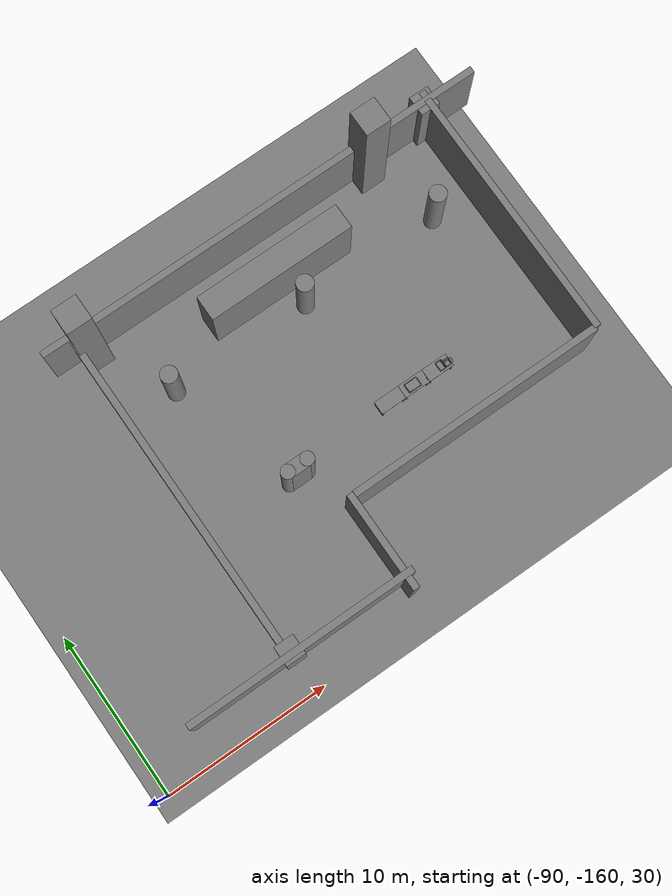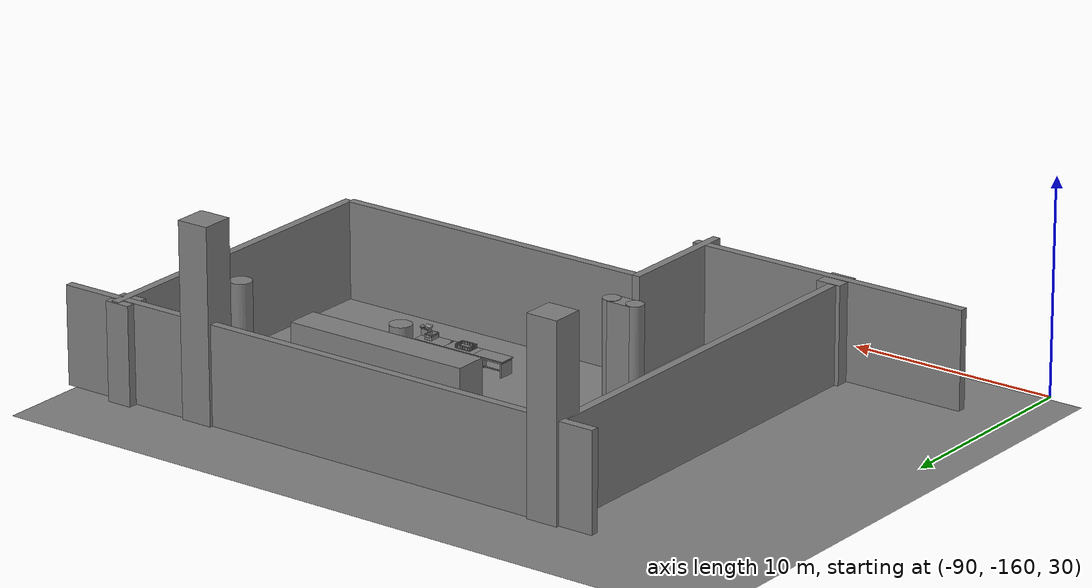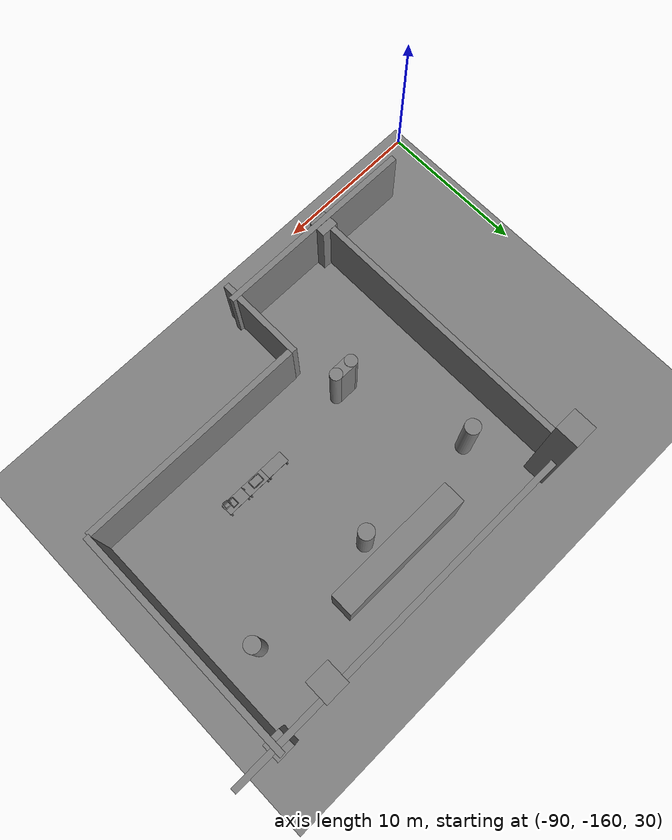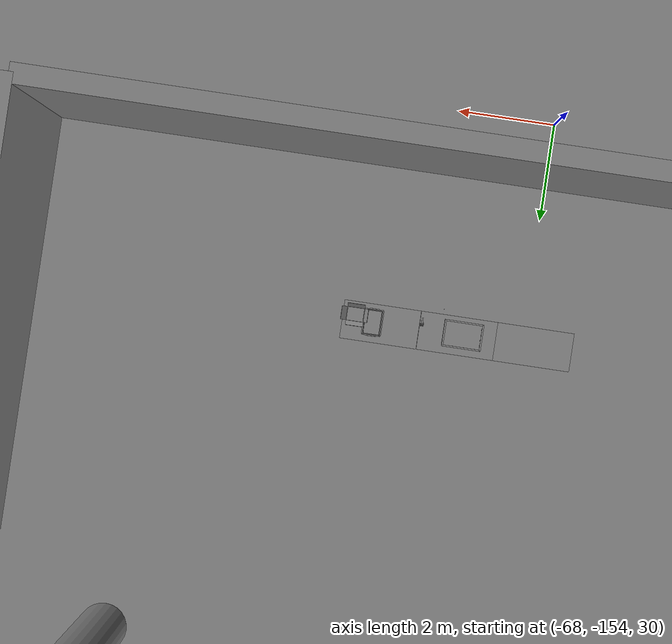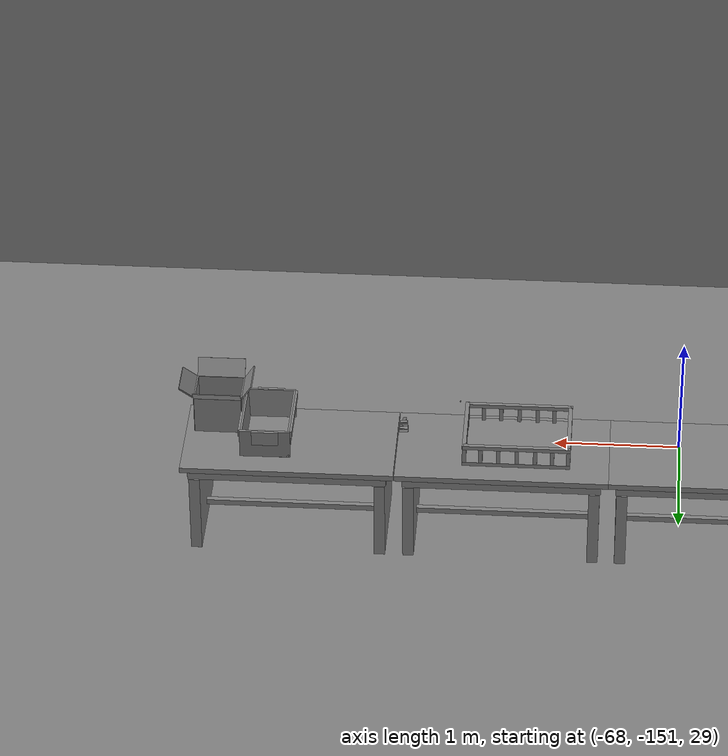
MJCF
<mujoco>
    <option gravity="0.000000000 0.000000000 -9.810000420" timestep="0.0049999999" integrator="implicitfast" density="1.225" viscosity="1.8000001e-05" noslip_iterations="10" iterations="100" sdf_iterations="50">
        <flag multiccd="disable"/>
    </option>
    <size memory="1000M"/>
    <compiler coordinate="local"/>
    <worldbody>
        <light cutoff="30" pos="0 1 1" dir="0 -1 -2"/>
        <light cutoff="30" pos="0 -1 1" dir="0 1 -2"/>
        <body pos="-64.866622925 -149.383972168 30.183746338" euler="89.999992371 89.999946594 0.000000000" name="openloong_gripper_2f85_fix_base_usda_bluebox_01">
            <geom contype="1" conaffinity="1" density="1000" type="box" material="" rgba="0.500000000 0.500000000 0.500000000 1.000000000" solimp="0.899999976 0.949999988 0.001000000" friction="1.000000000 0.005000000 0.000100000" solref="0.020000000 1.000000000" margin="0" condim="3" group="0" pos="0.276596069 0.187225342 0.000061035" quat="0.707107008 0.000077501 0.707106471 0.000077456" size="0.100000001 0.057999998 0.010000000" name="openloong_gripper_2f85_fix_base_usda_geom_1E8CA846_59CB_4A3F_8EAF_3471F24E04A5"/>
            <geom contype="1" conaffinity="1" density="1000" type="box" material="" rgba="0.500000000 0.500000000 0.500000000 1.000000000" solimp="0.899999976 0.949999988 0.001000000" friction="1.000000000 0.005000000 0.000100000" solref="0.020000000 1.000000000" margin="0" condim="3" group="0" pos="0.000000000 0.002883911 0.000000000" quat="1.000000000 0.000000000 0.000000000 0.000000000" size="0.254000008 0.003000000 0.172000006" name="openloong_gripper_2f85_fix_base_usda_geom_3468FF38_8CC5_45ED_BC9A_AAAF8571A2C6"/>
            <geom contype="1" conaffinity="1" density="1000" type="box" material="" rgba="0.500000000 0.500000000 0.500000000 1.000000000" solimp="0.899999976 0.949999988 0.001000000" friction="1.000000000 0.005000000 0.000100000" solref="0.020000000 1.000000000" margin="0" condim="3" group="0" pos="0.000015259 0.124874115 0.173477173" quat="0.999796450 0.020176515 -0.000000015 0.000000030" size="0.259999990 0.119999997 0.007000000" name="openloong_gripper_2f85_fix_base_usda_geom_D43466DF_118E_48A0_BA3F_6B704593D89E"/>
            <geom contype="1" conaffinity="1" density="1000" type="box" material="" rgba="0.500000000 0.500000000 0.500000000 1.000000000" solimp="0.899999976 0.949999988 0.001000000" friction="1.000000000 0.005000000 0.000100000" solref="0.020000000 1.000000000" margin="0" condim="3" group="0" pos="0.000015259 0.124874115 -0.173477173" quat="0.999796450 -0.020176545 -0.000000015 0.000000000" size="0.259999990 0.119999997 0.007000000" name="openloong_gripper_2f85_fix_base_usda_geom_78038C3F_8FC2_4294_99B9_7E2DB93A2582"/>
            <geom contype="1" conaffinity="1" density="1000" type="box" material="" rgba="0.500000000 0.500000000 0.500000000 1.000000000" solimp="0.899999976 0.949999988 0.001000000" friction="1.000000000 0.005000000 0.000100000" solref="0.020000000 1.000000000" margin="0" condim="3" group="0" pos="0.000015259 0.214012146 0.188980103" quat="0.999913096 0.013176724 0.000000015 0.000000000" size="0.259999990 0.029999999 0.012500000" name="openloong_gripper_2f85_fix_base_usda_geom_853BE4C5_FD0F_47BF_B9A8_8B81FA448A11"/>
            <geom contype="1" conaffinity="1" density="1000" type="box" material="" rgba="0.500000000 0.500000000 0.500000000 1.000000000" solimp="0.899999976 0.949999988 0.001000000" friction="1.000000000 0.005000000 0.000100000" solref="0.020000000 1.000000000" margin="0" condim="3" group="0" pos="-0.258346558 0.125289917 0.001876831" quat="0.702796996 -0.020792052 0.710783184 0.020769238" size="0.189999998 0.119999997 0.009000000" name="openloong_gripper_2f85_fix_base_usda_geom_3C4005E8_3F70_4619_921A_4B41565456EF"/>
            <geom contype="1" conaffinity="1" density="1000" type="box" material="" rgba="0.500000000 0.500000000 0.500000000 1.000000000" solimp="0.899999976 0.949999988 0.001000000" friction="1.000000000 0.005000000 0.000100000" solref="0.020000000 1.000000000" margin="0" condim="3" group="0" pos="0.000015259 0.214012146 -0.188980103" quat="0.999913096 -0.013176769 0.000000030 0.000000015" size="0.259999990 0.029999999 0.012500000" name="openloong_gripper_2f85_fix_base_usda_geom_356C29AD_3F91_40FD_8E7A_C7F6CB820775"/>
            <geom contype="1" conaffinity="1" density="1000" type="box" material="" rgba="0.500000000 0.500000000 0.500000000 1.000000000" solimp="0.899999976 0.949999988 0.001000000" friction="1.000000000 0.005000000 0.000100000" solref="0.020000000 1.000000000" margin="0" condim="3" group="0" pos="-0.276596069 0.187225342 0.000061035" quat="0.707106650 0.000077441 0.707106709 0.000077456" size="0.100000001 0.057999998 0.010000000" name="openloong_gripper_2f85_fix_base_usda_geom_27F4F9C9_76E7_4284_8976_1A5E9F96969B"/>
            <geom contype="1" conaffinity="1" density="1000" type="box" material="" rgba="0.500000000 0.500000000 0.500000000 1.000000000" solimp="0.899999976 0.949999988 0.001000000" friction="1.000000000 0.005000000 0.000100000" solref="0.020000000 1.000000000" margin="0" condim="3" group="0" pos="0.258346558 0.125289917 0.001876831" quat="0.702851534 0.018856451 0.710823834 -0.019329429" size="0.189999998 0.119999997 0.009000000" name="openloong_gripper_2f85_fix_base_usda_geom_F1A46E92_2DFA_47BE_99D1_4587DDBD3D9F"/>
            <freejoint name="openloong_gripper_2f85_fix_base_usda_bluebox_01_joint"/>
            <site size="0.005000000 0.005000000 0.005000000" rgba="0.500000000 0.500000000 0.500000000 1.000000000" pos="0.000000000 0.000000000 0.000000000" quat="0.999961913 0.008726534 0.000000000 0.000000000" group="0" type="sphere" name="openloong_gripper_2f85_fix_base_usda_bluebox_01site"/>
        </body>
        <body pos="-64.496299744 -149.491867065 30.235729218" euler="0.000000000 0.000000000 89.999946594" name="openloong_gripper_2f85_fix_base_usda_cardboardbox_01">
            <geom contype="1" conaffinity="1" density="1000" type="box" material="" rgba="0.500000000 0.500000000 0.500000000 1.000000000" solimp="0.899999976 0.949999988 0.001000000" friction="1.000000000 0.005000000 0.000100000" solref="0.020000000 1.000000000" margin="0" condim="3" group="0" pos="-0.003166199 -0.004086494 0.005052090" quat="1.000000000 0.000000000 0.000000000 0.000000000" size="0.142499998 0.177500010 0.005000000" name="openloong_gripper_2f85_fix_base_usda_geom_AFB887CB_04E1_41A8_A2B1_CB6B26136D39"/>
            <geom contype="1" conaffinity="1" density="1000" type="box" material="" rgba="0.500000000 0.500000000 0.500000000 1.000000000" solimp="0.899999976 0.949999988 0.001000000" friction="1.000000000 0.005000000 0.000100000" solref="0.020000000 1.000000000" margin="0" condim="3" group="0" pos="-0.003166199 0.170316696 0.150570869" quat="1.000000000 0.000000000 0.000000000 0.000000000" size="0.142499998 0.005000000 0.149999991" name="openloong_gripper_2f85_fix_base_usda_geom_BA77FA3B_81F4_4529_8D65_80D082A230FD"/>
            <geom contype="1" conaffinity="1" density="1000" type="box" material="" rgba="0.500000000 0.500000000 0.500000000 1.000000000" solimp="0.899999976 0.949999988 0.001000000" friction="1.000000000 0.005000000 0.000100000" solref="0.020000000 1.000000000" margin="0" condim="3" group="0" pos="-0.147399902 -0.005307198 0.150570869" quat="1.000000000 0.000000000 0.000000000 0.000000000" size="0.005000000 0.177500010 0.149999991" name="openloong_gripper_2f85_fix_base_usda_geom_C99D37CB_F2F5_44CC_B622_982F92435711"/>
            <geom contype="1" conaffinity="1" density="1000" type="box" material="" rgba="0.500000000 0.500000000 0.500000000 1.000000000" solimp="0.899999976 0.949999988 0.001000000" friction="1.000000000 0.005000000 0.000100000" solref="0.020000000 1.000000000" margin="0" condim="3" group="0" pos="0.140275955 -0.005307198 0.150570869" quat="1.000000000 0.000000000 0.000000000 0.000000000" size="0.005000000 0.177500010 0.149999991" name="openloong_gripper_2f85_fix_base_usda_geom_7EAD1EFD_6BE0_4333_A79B_ABB518E4CF7E"/>
            <geom contype="1" conaffinity="1" density="1000" type="box" material="" rgba="0.500000000 0.500000000 0.500000000 1.000000000" solimp="0.899999976 0.949999988 0.001000000" friction="1.000000000 0.005000000 0.000100000" solref="0.020000000 1.000000000" margin="0" condim="3" group="0" pos="-0.003166199 -0.181550980 0.150570869" quat="1.000000000 0.000000000 0.000000000 0.000000000" size="0.142499998 0.005000000 0.149999991" name="openloong_gripper_2f85_fix_base_usda_geom_7D9549DC_B787_405C_B2A0_C78267B20094"/>
            <freejoint name="openloong_gripper_2f85_fix_base_usda_cardboardbox_01_joint"/>
            <site size="0.005000000 0.005000000 0.005000000" rgba="0.500000000 0.500000000 0.500000000 1.000000000" pos="0.000000000 0.000000000 0.000000000" quat="0.999961913 0.008726535 0.000000000 0.000000000" group="0" type="sphere" name="openloong_gripper_2f85_fix_base_usda_site_EFBD1A08_1644_401D_B45E_9038762FDBCF"/>
            <body pos="0.139160156 -0.004048347 0.301930904" euler="-179.999954224 49.383502960 179.999954224" name="openloong_gripper_2f85_fix_base_usda_A1_006">
                <geom contype="1" conaffinity="1" density="1000" type="box" material="" rgba="0.500000000 0.500000000 0.500000000 1.000000000" solimp="0.899999976 0.949999988 0.001000000" friction="1.000000000 0.005000000 0.000100000" solref="0.020000000 1.000000000" margin="0" condim="3" group="0" pos="-0.071587563 0.000009537 0.001745224" quat="0.999999881 0.000000000 0.000000000 0.000000000" size="0.071249999 0.179999992 0.002500000" name="openloong_gripper_2f85_fix_base_usda_geom_2114D57B_B760_487B_95F8_BE76689CF1C8"/>
                <joint armature="0" stiffness="0.07" damping="0.0099999998" axis="0.000000 1.000000 0.000000" type="hinge" name="openloong_gripper_2f85_fix_base_usda_A1_006"/>
            </body>
            <body pos="-0.145902634 -0.004086494 0.301938057" euler="-180.000000000 -60.000011444 -180.000000000" name="openloong_gripper_2f85_fix_base_usda_A2_006">
                <geom contype="1" conaffinity="1" density="1000" type="box" material="" rgba="0.500000000 0.500000000 0.500000000 1.000000000" solimp="0.899999976 0.949999988 0.001000000" friction="1.000000000 0.005000000 0.000100000" solref="0.020000000 1.000000000" margin="0" condim="3" group="0" pos="0.071268082 0.000009537 0.002717972" quat="0.000002921 0.000000000 -0.000000030 0.999999881" size="0.071249999 0.179999992 0.002500000" name="openloong_gripper_2f85_fix_base_usda_geom_E8B438D1_69A3_41D4_8079_37CB472C9AD8"/>
                <joint armature="0" stiffness="0.07" damping="0.0099999998" axis="0.000000 1.000000 0.000000" type="hinge" name="openloong_gripper_2f85_fix_base_usda_A2_006"/>
            </body>
            <body pos="-0.003385544 0.175991058 0.301930904" euler="-125.858116150 -0.000004561 0.000002331" name="openloong_gripper_2f85_fix_base_usda_B2_006">
                <geom contype="1" conaffinity="1" density="1000" type="box" material="" rgba="0.500000000 0.500000000 0.500000000 1.000000000" solimp="0.899999976 0.949999988 0.001000000" friction="1.000000000 0.005000000 0.000100000" solref="0.020000000 1.000000000" margin="0" condim="3" group="0" pos="0.000009537 -0.070939064 -0.002470016" quat="0.999614120 0.027776197 -0.000000015 0.000000030" size="0.137500003 0.064999998 0.005000000" name="openloong_gripper_2f85_fix_base_usda_geom_3A765D56_B8D2_410E_940C_0259967A6F80"/>
                <joint armature="0" stiffness="0.07" damping="0.0099999998" axis="1.000000 0.000000 0.000000" type="hinge" name="openloong_gripper_2f85_fix_base_usda_B2_006"/>
            </body>
            <body pos="-0.003385544 -0.184140205 0.301938057" euler="147.805557251 0.000000000 0.000000000" name="openloong_gripper_2f85_fix_base_usda_B1_006">
                <geom contype="1" conaffinity="1" density="1000" type="box" material="" rgba="0.500000000 0.500000000 0.500000000 1.000000000" solimp="0.899999976 0.949999988 0.001000000" friction="1.000000000 0.005000000 0.000100000" solref="0.020000000 1.000000000" margin="0" condim="3" group="0" pos="-0.000028610 0.070202351 -0.002703667" quat="0.999614179 -0.027776167 0.000000000 0.000000000" size="0.137500003 0.064999998 0.005000000" name="openloong_gripper_2f85_fix_base_usda_geom_5E2C42D2_C78A_4D58_9F23_00345A8A5C09"/>
                <joint armature="0" stiffness="0.07" damping="0.0099999998" axis="1.000000 0.000000 0.000000" type="hinge" name="openloong_gripper_2f85_fix_base_usda_B1_006"/>
            </body>
        </body>
        <body pos="-65.882858276 -149.481979370 30.229999542" euler="-64.487716675 0.000000000 0.000000000" name="openloong_gripper_2f85_fix_base_usda_Barcode">
            <geom contype="1" conaffinity="1" density="1000" type="box" material="" rgba="0.500000000 0.500000000 0.500000000 1.000000000" solimp="0.899999976 0.949999988 0.001000000" friction="1.000000000 0.005000000 0.000100000" solref="0.020000000 1.000000000" margin="0" condim="3" group="0" pos="0.000000000 0.013038635 0.001419067" quat="0.000000000 0.000000000 0.000000000 1.000000119" size="0.034000002 0.010000000 0.017999999" name="openloong_gripper_2f85_fix_base_usda_geom_C76BEAB2_3F13_45C5_8963_E6EF23575FE4"/>
            <geom contype="1" conaffinity="1" density="1000" type="box" material="" rgba="0.500000000 0.500000000 0.500000000 1.000000000" solimp="0.899999976 0.949999988 0.001000000" friction="1.000000000 0.005000000 0.000100000" solref="0.020000000 1.000000000" margin="0" condim="3" group="0" pos="0.000000000 -0.035301208 -0.007095337" quat="0.000000000 0.000000000 -0.043619365 0.999048233" size="0.028999999 0.010000000 0.020000000" name="openloong_gripper_2f85_fix_base_usda_geom_91E00D20_813B_435B_BBB2_823E3898E6FD"/>
            <geom contype="1" conaffinity="1" density="1000" type="box" material="" rgba="0.500000000 0.500000000 0.500000000 1.000000000" solimp="0.899999976 0.949999988 0.001000000" friction="1.000000000 0.005000000 0.000100000" solref="0.020000000 1.000000000" margin="0" condim="3" group="0" pos="0.000000000 -0.043411255 -0.011749268" quat="0.922262907 0.386563420 0.000000000 0.000000000" size="0.026000001 0.010000000 0.020000000" name="openloong_gripper_2f85_fix_base_usda_geom_746CE888_4A10_40D2_A862_F4C439BCE5C2"/>
            <geom contype="1" conaffinity="1" density="1000" type="box" material="" rgba="0.500000000 0.500000000 0.500000000 1.000000000" solimp="0.899999976 0.949999988 0.001000000" friction="1.000000000 0.005000000 0.000100000" solref="0.020000000 1.000000000" margin="0" condim="3" group="0" pos="0.000000000 -0.016967773 -0.031860352" quat="0.000000000 0.000000000 0.000000000 1.000000119" size="0.008000000 0.010000000 0.013000000" name="openloong_gripper_2f85_fix_base_usda_geom_5CA1B249_E683_4E4C_A08F_AE7896A3BDC6"/>
            <geom contype="1" conaffinity="1" density="1000" type="box" material="" rgba="0.500000000 0.500000000 0.500000000 1.000000000" solimp="0.899999976 0.949999988 0.001000000" friction="1.000000000 0.005000000 0.000100000" solref="0.020000000 1.000000000" margin="0" condim="3" group="0" pos="0.000000000 -0.001869202 0.000312805" quat="0.953716993 0.300705761 0.000000000 0.000000000" size="0.032000002 0.010000000 0.018999999" name="openloong_gripper_2f85_fix_base_usda_geom_B7CA0BD7_BF98_4CEE_95C3_E10CC3C3A11A"/>
            <geom contype="1" conaffinity="1" density="1000" type="box" material="" rgba="0.500000000 0.500000000 0.500000000 1.000000000" solimp="0.899999976 0.949999988 0.001000000" friction="1.000000000 0.005000000 0.000100000" solref="0.020000000 1.000000000" margin="0" condim="3" group="0" pos="0.000000000 -0.019531250 -0.003173828" quat="0.953716993 0.300705761 0.000000000 0.000000000" size="0.030999999 0.010000000 0.020000000" name="openloong_gripper_2f85_fix_base_usda_geom_81C3AD28_7962_4809_A4B3_DA1755EB022D"/>
            <geom contype="1" conaffinity="1" density="1000" type="box" material="" rgba="0.500000000 0.500000000 0.500000000 1.000000000" solimp="0.899999976 0.949999988 0.001000000" friction="1.000000000 0.005000000 0.000100000" solref="0.020000000 1.000000000" margin="0" condim="3" group="0" pos="0.000000000 -0.035301208 -0.007095337" quat="0.953716993 0.300705761 0.000000000 0.000000000" size="0.028999999 0.010000000 0.020000000" name="openloong_gripper_2f85_fix_base_usda_geom_017F3F1E_2B08_49E4_973C_C1136B5A4FD6"/>
            <geom contype="1" conaffinity="1" density="1000" type="box" material="" rgba="0.500000000 0.500000000 0.500000000 1.000000000" solimp="0.899999976 0.949999988 0.001000000" friction="1.000000000 0.005000000 0.000100000" solref="0.020000000 1.000000000" margin="0" condim="3" group="0" pos="0.000000000 -0.042617798 -0.071121216" quat="0.000000000 0.000000000 0.000000000 1.000000119" size="0.013000000 0.021000000 0.059999999" name="openloong_gripper_2f85_fix_base_usda_geom_23DD9D96_C643_4DA6_B8BF_634318DEA6A5"/>
            <freejoint name="openloong_gripper_2f85_fix_base_usda_Barcode_joint"/>
            <site size="0.005000000 0.005000000 0.005000000" rgba="0.500000000 0.500000000 0.500000000 1.000000000" pos="0.000000000 0.000000000 0.000000000" quat="1.000000000 0.000000000 0.000000000 0.000000000" group="0" type="sphere" name="openloong_gripper_2f85_fix_base_usda_Barcode_site"/>
        </body>
        <body pos="-66.745018005 -149.392349243 30.184000015" euler="0.000000000 0.000000000 89.999946594" name="[22329717913003]_Basket_01">
            <geom contype="1" conaffinity="1" density="1000" type="box" material="" rgba="0.500000000 0.500000000 0.500000000 1.000000000" solimp="0.899999976 0.949999988 0.001000000" friction="1.000000000 0.005000000 0.000100000" solref="0.020000000 1.000000000" margin="0" condim="3" group="0" pos="-0.052425385 0.389207840 0.089787483" quat="0.707107008 0.000000000 0.000000000 0.707106411" size="0.014249999 0.014249999 0.059999999" name="[22329717913003]_geom_8E93D50F_A84F_4754_99AA_DF61EAA1972F"/>
            <geom contype="1" conaffinity="1" density="1000" type="box" material="" rgba="0.500000000 0.500000000 0.500000000 1.000000000" solimp="0.899999976 0.949999988 0.001000000" friction="1.000000000 0.005000000 0.000100000" solref="0.020000000 1.000000000" margin="0" condim="3" group="0" pos="0.264015198 -0.133043289 0.089787483" quat="0.707107008 0.000000000 0.000000000 0.707106411" size="0.014249999 0.014249999 0.059999999" name="[22329717913003]_geom_D3155430_BE7E_44DA_A3E1_B565E1F1151C"/>
            <geom contype="1" conaffinity="1" density="1000" type="box" material="" rgba="0.500000000 0.500000000 0.500000000 1.000000000" solimp="0.899999976 0.949999988 0.001000000" friction="1.000000000 0.005000000 0.000100000" solref="0.020000000 1.000000000" margin="0" condim="3" group="0" pos="-0.264015198 -0.265548706 0.089793205" quat="0.707107008 0.000000000 0.000000000 0.707106411" size="0.014249999 0.014249999 0.059999999" name="[22329717913003]_geom_D5659F0F_E7BE_4302_935C_B0736C01D168"/>
            <geom contype="1" conaffinity="1" density="1000" type="box" material="" rgba="0.500000000 0.500000000 0.500000000 1.000000000" solimp="0.899999976 0.949999988 0.001000000" friction="1.000000000 0.005000000 0.000100000" solref="0.020000000 1.000000000" margin="0" condim="3" group="0" pos="-0.160263062 -0.389322281 0.089793205" quat="0.707107008 0.000000000 0.000000000 0.707106411" size="0.014249999 0.014249999 0.059999999" name="[22329717913003]_geom_4302AFB2_0938_4163_BDAF_4637618C3D56"/>
            <geom contype="1" conaffinity="1" density="1000" type="box" material="" rgba="0.500000000 0.500000000 0.500000000 1.000000000" solimp="0.899999976 0.949999988 0.001000000" friction="1.000000000 0.005000000 0.000100000" solref="0.020000000 1.000000000" margin="0" condim="3" group="0" pos="0.162265778 -0.389322281 0.089787483" quat="0.707107008 0.000000000 0.000000000 0.707106411" size="0.014249999 0.014249999 0.059999999" name="[22329717913003]_geom_276AB1FF_427A_40C8_84B1_063B599D1D51"/>
            <geom contype="1" conaffinity="1" density="1000" type="box" material="" rgba="0.500000000 0.500000000 0.500000000 1.000000000" solimp="0.899999976 0.949999988 0.001000000" friction="1.000000000 0.005000000 0.000100000" solref="0.020000000 1.000000000" margin="0" condim="3" group="0" pos="0.264015198 0.389207840 0.089787483" quat="0.707107008 0.000000000 0.000000000 0.707106411" size="0.014249999 0.014249999 0.059999999" name="[22329717913003]_geom_29ECF54D_C020_40A5_BD9E_9A122954470E"/>
            <geom contype="1" conaffinity="1" density="1000" type="box" material="" rgba="0.500000000 0.500000000 0.500000000 1.000000000" solimp="0.899999976 0.949999988 0.001000000" friction="1.000000000 0.005000000 0.000100000" solref="0.020000000 1.000000000" margin="0" condim="3" group="0" pos="-0.264015198 -0.133043289 0.089793205" quat="0.707107008 0.000000000 0.000000000 0.707106411" size="0.014249999 0.014249999 0.059999999" name="[22329717913003]_geom_9EDD9F82_5CAC_442D_9ACD_E7E29138A137"/>
            <geom contype="1" conaffinity="1" density="1000" type="box" material="" rgba="0.500000000 0.500000000 0.500000000 1.000000000" solimp="0.899999976 0.949999988 0.001000000" friction="1.000000000 0.005000000 0.000100000" solref="0.020000000 1.000000000" margin="0" condim="3" group="0" pos="-0.264026642 0.269256592 0.089793205" quat="0.707107008 0.000000000 0.000000000 0.707106411" size="0.014249999 0.014249999 0.059999999" name="[22329717913003]_geom_679CDC28_0D52_474C_BCE1_0EA88B4D447F"/>
            <geom contype="1" conaffinity="1" density="1000" type="box" material="" rgba="0.500000000 0.500000000 0.500000000 1.000000000" solimp="0.899999976 0.949999988 0.001000000" friction="1.000000000 0.005000000 0.000100000" solref="0.020000000 1.000000000" margin="0" condim="3" group="0" pos="0.054462433 0.389207840 0.089787483" quat="0.707107008 0.000000000 0.000000000 0.707106411" size="0.014249999 0.014249999 0.059999999" name="[22329717913003]_geom_8F17B51F_71F4_4A59_A577_6AF6DD4EA1D0"/>
            <geom contype="1" conaffinity="1" density="1000" type="box" material="" rgba="0.500000000 0.500000000 0.500000000 1.000000000" solimp="0.899999976 0.949999988 0.001000000" friction="1.000000000 0.005000000 0.000100000" solref="0.020000000 1.000000000" margin="0" condim="3" group="0" pos="0.054462433 -0.389322281 0.089787483" quat="0.707107008 0.000000000 0.000000000 0.707106411" size="0.014249999 0.014249999 0.059999999" name="[22329717913003]_geom_200F3E1F_C20B_44E2_B28D_FE60D18A1422"/>
            <geom contype="1" conaffinity="1" density="1000" type="box" material="" rgba="0.500000000 0.500000000 0.500000000 1.000000000" solimp="0.899999976 0.949999988 0.001000000" friction="1.000000000 0.005000000 0.000100000" solref="0.020000000 1.000000000" margin="0" condim="3" group="0" pos="0.264015198 0.269256592 0.089793205" quat="0.707107008 0.000000000 0.000000000 0.707106411" size="0.014249999 0.014249999 0.059999999" name="[22329717913003]_geom_B28DFB41_CAF7_4B8E_9BD3_D168FD1405FC"/>
            <geom contype="1" conaffinity="1" density="1000" type="box" material="" rgba="0.500000000 0.500000000 0.500000000 1.000000000" solimp="0.899999976 0.949999988 0.001000000" friction="1.000000000 0.005000000 0.000100000" solref="0.020000000 1.000000000" margin="0" condim="3" group="0" pos="0.264015198 -0.389322281 0.089787483" quat="0.707107008 0.000000000 0.000000000 0.707106411" size="0.014249999 0.014249999 0.059999999" name="[22329717913003]_geom_3E33F0A0_9F5E_437B_B8CB_42D2CAF83C66"/>
            <geom contype="1" conaffinity="1" density="1000" type="box" material="" rgba="0.500000000 0.500000000 0.500000000 1.000000000" solimp="0.899999976 0.949999988 0.001000000" friction="1.000000000 0.005000000 0.000100000" solref="0.020000000 1.000000000" margin="0" condim="3" group="0" pos="0.000000000 0.000000000 0.015998840" quat="0.707107008 0.000000000 0.000000000 0.707106411" size="0.403499991 0.279000014 0.015750000" name="[22329717913003]_geom_AE9CC62A_7410_4902_BD8E_A6E269636108"/>
            <geom contype="1" conaffinity="1" density="1000" type="box" material="" rgba="0.500000000 0.500000000 0.500000000 1.000000000" solimp="0.899999976 0.949999988 0.001000000" friction="1.000000000 0.005000000 0.000100000" solref="0.020000000 1.000000000" margin="0" condim="3" group="0" pos="0.000000000 -0.389476776 0.163619041" quat="0.707107008 0.000000000 0.000000000 0.707106411" size="0.015000000 0.277500004 0.015750000" name="[22329717913003]_geom_4520BCE7_9A6F_4732_8151_FD83DF8A79D4"/>
            <geom contype="1" conaffinity="1" density="1000" type="box" material="" rgba="0.500000000 0.500000000 0.500000000 1.000000000" solimp="0.899999976 0.949999988 0.001000000" friction="1.000000000 0.005000000 0.000100000" solref="0.020000000 1.000000000" margin="0" condim="3" group="0" pos="0.162265778 0.389207840 0.089787483" quat="0.707107008 0.000000000 0.000000000 0.707106411" size="0.014249999 0.014249999 0.059999999" name="[22329717913003]_geom_5FCCB1D7_9CAD_40D8_B897_B7297DAAC26C"/>
            <geom contype="1" conaffinity="1" density="1000" type="box" material="" rgba="0.500000000 0.500000000 0.500000000 1.000000000" solimp="0.899999976 0.949999988 0.001000000" friction="1.000000000 0.005000000 0.000100000" solref="0.020000000 1.000000000" margin="0" condim="3" group="0" pos="0.000000000 0.389471054 0.163619041" quat="0.707107008 0.000000000 0.000000000 0.707106411" size="0.015000000 0.277500004 0.015750000" name="[22329717913003]_geom_EABD1632_1181_4509_BC60_E7D1DF896AC4"/>
            <geom contype="1" conaffinity="1" density="1000" type="box" material="" rgba="0.500000000 0.500000000 0.500000000 1.000000000" solimp="0.899999976 0.949999988 0.001000000" friction="1.000000000 0.005000000 0.000100000" solref="0.020000000 1.000000000" margin="0" condim="3" group="0" pos="-0.263511658 0.000000000 0.163619041" quat="0.707107008 0.000000000 0.000000000 0.707106411" size="0.403499991 0.015000000 0.015750000" name="[22329717913003]_geom_1DA9FB09_ABED_4572_A479_83A70520481D"/>
            <geom contype="1" conaffinity="1" density="1000" type="box" material="" rgba="0.500000000 0.500000000 0.500000000 1.000000000" solimp="0.899999976 0.949999988 0.001000000" friction="1.000000000 0.005000000 0.000100000" solref="0.020000000 1.000000000" margin="0" condim="3" group="0" pos="-0.264015198 0.141334534 0.089793205" quat="0.707107008 0.000000000 0.000000000 0.707106411" size="0.014249999 0.014249999 0.059999999" name="[22329717913003]_geom_EC9DCFD2_3C26_47AA_95D9_B0E271D22DEE"/>
            <geom contype="1" conaffinity="1" density="1000" type="box" material="" rgba="0.500000000 0.500000000 0.500000000 1.000000000" solimp="0.899999976 0.949999988 0.001000000" friction="1.000000000 0.005000000 0.000100000" solref="0.020000000 1.000000000" margin="0" condim="3" group="0" pos="0.264015198 -0.265548706 0.089787483" quat="0.707107008 0.000000000 0.000000000 0.707106411" size="0.014249999 0.014249999 0.059999999" name="[22329717913003]_geom_B94815B2_E13D_4F82_B26B_B065C11ED0C1"/>
            <geom contype="1" conaffinity="1" density="1000" type="box" material="" rgba="0.500000000 0.500000000 0.500000000 1.000000000" solimp="0.899999976 0.949999988 0.001000000" friction="1.000000000 0.005000000 0.000100000" solref="0.020000000 1.000000000" margin="0" condim="3" group="0" pos="-0.160263062 0.389207840 0.089787483" quat="0.707107008 0.000000000 0.000000000 0.707106411" size="0.014249999 0.014249999 0.059999999" name="[22329717913003]_geom_D64AC78A_213D_4993_934A_767761121FE9"/>
            <geom contype="1" conaffinity="1" density="1000" type="box" material="" rgba="0.500000000 0.500000000 0.500000000 1.000000000" solimp="0.899999976 0.949999988 0.001000000" friction="1.000000000 0.005000000 0.000100000" solref="0.020000000 1.000000000" margin="0" condim="3" group="0" pos="-0.052425385 -0.389322281 0.089787483" quat="0.707107008 0.000000000 0.000000000 0.707106411" size="0.014249999 0.014249999 0.059999999" name="[22329717913003]_geom_C4FBC7A8_EDAF_4C20_912F_8E8BECE45087"/>
            <geom contype="1" conaffinity="1" density="1000" type="box" material="" rgba="0.500000000 0.500000000 0.500000000 1.000000000" solimp="0.899999976 0.949999988 0.001000000" friction="1.000000000 0.005000000 0.000100000" solref="0.020000000 1.000000000" margin="0" condim="3" group="0" pos="-0.264026642 -0.389322281 0.089793205" quat="0.707107008 0.000000000 0.000000000 0.707106411" size="0.014249999 0.014249999 0.059999999" name="[22329717913003]_geom_8FF1EEA7_5B86_4D84_8595_9065F9452FCC"/>
            <geom contype="1" conaffinity="1" density="1000" type="box" material="" rgba="0.500000000 0.500000000 0.500000000 1.000000000" solimp="0.899999976 0.949999988 0.001000000" friction="1.000000000 0.005000000 0.000100000" solref="0.020000000 1.000000000" margin="0" condim="3" group="0" pos="0.264015198 0.141334534 0.089787483" quat="0.707107008 0.000000000 0.000000000 0.707106411" size="0.014249999 0.014249999 0.059999999" name="[22329717913003]_geom_D5556515_5643_4593_8A1E_5EAA304C5475"/>
            <geom contype="1" conaffinity="1" density="1000" type="box" material="" rgba="0.500000000 0.500000000 0.500000000 1.000000000" solimp="0.899999976 0.949999988 0.001000000" friction="1.000000000 0.005000000 0.000100000" solref="0.020000000 1.000000000" margin="0" condim="3" group="0" pos="-0.264015198 0.389207840 0.089793205" quat="0.707107008 0.000000000 0.000000000 0.707106411" size="0.014249999 0.014249999 0.059999999" name="[22329717913003]_geom_DEEFB492_FB6F_4B6D_8C68_D45688C76D41"/>
            <geom contype="1" conaffinity="1" density="1000" type="box" material="" rgba="0.500000000 0.500000000 0.500000000 1.000000000" solimp="0.899999976 0.949999988 0.001000000" friction="1.000000000 0.005000000 0.000100000" solref="0.020000000 1.000000000" margin="0" condim="3" group="0" pos="0.264015198 0.004480362 0.089787483" quat="0.707107008 0.000000000 0.000000000 0.707106411" size="0.014249999 0.014249999 0.059999999" name="[22329717913003]_geom_438FD673_E894_44C4_90F5_0A3A4041031A"/>
            <geom contype="1" conaffinity="1" density="1000" type="box" material="" rgba="0.500000000 0.500000000 0.500000000 1.000000000" solimp="0.899999976 0.949999988 0.001000000" friction="1.000000000 0.005000000 0.000100000" solref="0.020000000 1.000000000" margin="0" condim="3" group="0" pos="0.263694763 -0.000011444 0.163619041" quat="0.707107008 0.000000000 0.000000000 0.707106411" size="0.403499991 0.015000000 0.015750000" name="[22329717913003]_geom_67813228_E637_47C2_B8E5_D27C739096DC"/>
            <geom contype="1" conaffinity="1" density="1000" type="box" material="" rgba="0.500000000 0.500000000 0.500000000 1.000000000" solimp="0.899999976 0.949999988 0.001000000" friction="1.000000000 0.005000000 0.000100000" solref="0.020000000 1.000000000" margin="0" condim="3" group="0" pos="-0.264015198 0.004480362 0.089793205" quat="0.707107008 0.000000000 0.000000000 0.707106411" size="0.014249999 0.014249999 0.059999999" name="[22329717913003]_geom_179FA272_5680_4DAB_B5E9_4E2A2FB4A12A"/>
            <freejoint name="[22329717913003]_joint_E26EA774_5150_46B1_BABE_17DA2317A804"/>
        </body>
        <body pos="0.000000000 0.000000000 0.000000000" euler="0.000000000 0.000000000 0.000000000" name="Static Objects_Static Objects">
            <geom contype="1" conaffinity="1" density="1000" type="box" material="" rgba="0.500000000 0.500000000 0.500000000 1.000000000" solimp="0.899999976 0.949999988 0.001000000" friction="1.000000000 0.005000000 0.000100000" solref="0.020000000 1.000000000" margin="0" condim="3" group="0" pos="-67.544113159 -149.365814209 29.727830887" quat="0.500000417 0.499999970 0.499999553 0.499999970" size="0.381000012 0.319999993 0.041000001" name="Static Objects_geom_CDE4A1A2_D0EF_4CA1_8969_A06D55FDE654"/>
            <geom contype="1" conaffinity="1" density="1000" type="box" material="" rgba="0.500000000 0.500000000 0.500000000 1.000000000" solimp="0.899999976 0.949999988 0.001000000" friction="1.000000000 0.005000000 0.000100000" solref="0.020000000 1.000000000" margin="0" condim="3" group="0" pos="-68.239501953 -149.365814209 30.086868286" quat="0.500000417 0.499999970 0.499999553 0.499999970" size="0.370999992 0.039500002 0.745000005" name="Static Objects_geom_9036B8C7_CCD0_422B_966A_C049106E9C43"/>
            <geom contype="1" conaffinity="1" density="1000" type="box" material="" rgba="0.500000000 0.500000000 0.500000000 1.000000000" solimp="0.899999976 0.949999988 0.001000000" friction="1.000000000 0.005000000 0.000100000" solref="0.020000000 1.000000000" margin="0" condim="3" group="0" pos="-68.239501953 -149.365814209 30.147235870" quat="0.500000417 0.499999970 0.499999553 0.499999970" size="0.400000006 0.022000000 0.800000012" name="Static Objects_geom_E477B93E_F34A_4B8B_BF86_A58421D3B724"/>
            <geom contype="1" conaffinity="1" density="1000" type="box" material="" rgba="0.500000000 0.500000000 0.500000000 1.000000000" solimp="0.899999976 0.949999988 0.001000000" friction="1.000000000 0.005000000 0.000100000" solref="0.020000000 1.000000000" margin="0" condim="3" group="0" pos="-68.934890747 -149.365814209 29.727830887" quat="0.500000417 0.499999970 0.499999553 0.499999970" size="0.381000012 0.319999993 0.041000001" name="Static Objects_geom_03A5FE42_F67D_45ED_93DC_B5E6A35CC16E"/>
            <geom contype="1" conaffinity="1" density="1000" type="box" material="" rgba="0.500000000 0.500000000 0.500000000 1.000000000" solimp="0.899999976 0.949999988 0.001000000" friction="1.000000000 0.005000000 0.000100000" solref="0.020000000 1.000000000" margin="0" condim="3" group="0" pos="-68.239501953 -149.365814209 29.561563492" quat="0.500000417 0.499999970 0.499999553 0.499999970" size="0.020000000 0.022000000 0.660000026" name="Static Objects_geom_DBBE8032_4D37_49AE_9EC4_D2B9634C7B07"/>
            <geom contype="1" conaffinity="1" density="1000" type="box" material="" rgba="0.500000000 0.500000000 0.500000000 1.000000000" solimp="0.899999976 0.949999988 0.001000000" friction="1.000000000 0.005000000 0.000100000" solref="0.020000000 1.000000000" margin="0" condim="3" group="0" pos="-65.945671082 -149.365814209 29.727830887" quat="0.500000417 0.499999970 0.499999553 0.499999970" size="0.381000012 0.319999993 0.041000001" name="Static Objects_geom_7A69B019_DB04_454C_94C6_1B24C6E71967"/>
            <geom contype="1" conaffinity="1" density="1000" type="box" material="" rgba="0.500000000 0.500000000 0.500000000 1.000000000" solimp="0.899999976 0.949999988 0.001000000" friction="1.000000000 0.005000000 0.000100000" solref="0.020000000 1.000000000" margin="0" condim="3" group="0" pos="-66.641059875 -149.365814209 30.086868286" quat="0.500000417 0.499999970 0.499999553 0.499999970" size="0.370999992 0.039500002 0.745000005" name="Static Objects_geom_7744BE4E_40D7_4825_8D9A_AA80B7FF8090"/>
            <geom contype="1" conaffinity="1" density="1000" type="box" material="" rgba="0.500000000 0.500000000 0.500000000 1.000000000" solimp="0.899999976 0.949999988 0.001000000" friction="1.000000000 0.005000000 0.000100000" solref="0.020000000 1.000000000" margin="0" condim="3" group="0" pos="-66.641059875 -149.365814209 30.147235870" quat="0.500000417 0.499999970 0.499999553 0.499999970" size="0.400000006 0.022000000 0.800000012" name="Static Objects_geom_81724B03_D90C_444A_A8C7_955B571CD53F"/>
            <geom contype="1" conaffinity="1" density="1000" type="box" material="" rgba="0.500000000 0.500000000 0.500000000 1.000000000" solimp="0.899999976 0.949999988 0.001000000" friction="1.000000000 0.005000000 0.000100000" solref="0.020000000 1.000000000" margin="0" condim="3" group="0" pos="-67.336448669 -149.365814209 29.727830887" quat="0.500000417 0.499999970 0.499999553 0.499999970" size="0.381000012 0.319999993 0.041000001" name="Static Objects_geom_44D4E8E5_FD64_41E0_BA6C_DE36A90C31FA"/>
            <geom contype="1" conaffinity="1" density="1000" type="box" material="" rgba="0.500000000 0.500000000 0.500000000 1.000000000" solimp="0.899999976 0.949999988 0.001000000" friction="1.000000000 0.005000000 0.000100000" solref="0.020000000 1.000000000" margin="0" condim="3" group="0" pos="-66.641059875 -149.365814209 29.561563492" quat="0.500000417 0.499999970 0.499999553 0.499999970" size="0.020000000 0.022000000 0.660000026" name="Static Objects_geom_0FE1CFC1_860F_4B86_939C_DE8974EA9E8D"/>
            <geom contype="1" conaffinity="1" density="1000" type="box" material="" rgba="0.500000000 0.500000000 0.500000000 1.000000000" solimp="0.899999976 0.949999988 0.001000000" friction="1.000000000 0.005000000 0.000100000" solref="0.020000000 1.000000000" margin="0" condim="3" group="0" pos="-64.338577271 -149.365814209 29.727830887" quat="0.500000417 0.499999970 0.499999553 0.499999970" size="0.381000012 0.319999993 0.041000001" name="Static Objects_geom_0D3F9F7F_AD3F_4A44_BE2B_EC3B1C857EBC"/>
            <geom contype="1" conaffinity="1" density="1000" type="box" material="" rgba="0.500000000 0.500000000 0.500000000 1.000000000" solimp="0.899999976 0.949999988 0.001000000" friction="1.000000000 0.005000000 0.000100000" solref="0.020000000 1.000000000" margin="0" condim="3" group="0" pos="-65.033966064 -149.365814209 30.086868286" quat="0.500000417 0.499999970 0.499999553 0.499999970" size="0.370999992 0.039500002 0.745000005" name="Static Objects_geom_27AFE239_5884_41BE_A90D_D45D9276199E"/>
            <geom contype="1" conaffinity="1" density="1000" type="box" material="" rgba="0.500000000 0.500000000 0.500000000 1.000000000" solimp="0.899999976 0.949999988 0.001000000" friction="1.000000000 0.005000000 0.000100000" solref="0.020000000 1.000000000" margin="0" condim="3" group="0" pos="-65.033966064 -149.365814209 30.147235870" quat="0.500000417 0.499999970 0.499999553 0.499999970" size="0.400000006 0.022000000 0.800000012" name="Static Objects_geom_8E67E03B_58FA_4D00_9265_E54B94CFA42F"/>
            <geom contype="1" conaffinity="1" density="1000" type="box" material="" rgba="0.500000000 0.500000000 0.500000000 1.000000000" solimp="0.899999976 0.949999988 0.001000000" friction="1.000000000 0.005000000 0.000100000" solref="0.020000000 1.000000000" margin="0" condim="3" group="0" pos="-65.729354858 -149.365814209 29.727830887" quat="0.500000417 0.499999970 0.499999553 0.499999970" size="0.381000012 0.319999993 0.041000001" name="Static Objects_geom_1786B32F_2F15_4329_8982_01FA9A7A10E0"/>
            <geom contype="1" conaffinity="1" density="1000" type="box" material="" rgba="0.500000000 0.500000000 0.500000000 1.000000000" solimp="0.899999976 0.949999988 0.001000000" friction="1.000000000 0.005000000 0.000100000" solref="0.020000000 1.000000000" margin="0" condim="3" group="0" pos="-65.033966064 -149.365814209 29.561563492" quat="0.500000417 0.499999970 0.499999553 0.499999970" size="0.020000000 0.022000000 0.660000026" name="Static Objects_geom_2A427FC3_72BA_4E44_9AE6_B05A375C14AB"/>
            <geom contype="1" conaffinity="1" density="1000" type="box" material="" rgba="0.500000000 0.500000000 0.500000000 1.000000000" solimp="0.899999976 0.949999988 0.001000000" friction="1.000000000 0.005000000 0.000100000" solref="0.020000000 1.000000000" margin="0" condim="3" group="0" pos="-61.754566193 -137.853729248 33.906845093" quat="0.707107067 0.000000000 0.000000000 0.707106471" size="0.759999990 0.759999990 4.500000000" name="Static Objects_geom_0B1D9A56_80C8_46D4_9489_5546261C60BA"/>
            <geom contype="1" conaffinity="1" density="1000" type="box" material="" rgba="0.500000000 0.500000000 0.500000000 1.000000000" solimp="0.899999976 0.949999988 0.001000000" friction="1.000000000 0.005000000 0.000100000" solref="0.020000000 1.000000000" margin="0" condim="3" group="0" pos="-57.511135101 -144.927108765 31.707921982" quat="1.000000000 0.000000000 0.000000000 0.000000000" size="0.200000003 8.000000000 2.299999952" name="Static Objects_geom_2B7D8273_291C_4C50_834E_A466E9DF5733"/>
            <geom contype="1" conaffinity="1" density="1000" type="box" material="" rgba="0.500000000 0.500000000 0.500000000 1.000000000" solimp="0.899999976 0.949999988 0.001000000" friction="1.000000000 0.005000000 0.000100000" solref="0.020000000 1.000000000" margin="0" condim="3" group="0" pos="-80.517646790 -157.574050903 31.688196182" quat="0.707107067 0.000000000 0.000000000 0.707106471" size="0.600000024 0.600000024 2.299999952" name="Static Objects_geom_6BF5F77F_C1E8_44C1_8589_FD6B01D5C9CE"/>
            <geom contype="1" conaffinity="1" density="1000" type="box" material="" rgba="0.500000000 0.500000000 0.500000000 1.000000000" solimp="0.899999976 0.949999988 0.001000000" friction="1.000000000 0.005000000 0.000100000" solref="0.020000000 1.000000000" margin="0" condim="3" group="0" pos="-80.711044312 -147.414932251 31.666158676" quat="1.000000000 0.000000000 0.000000000 0.000000000" size="0.200000003 10.000000000 2.299999952" name="Static Objects_geom_5C1045DD_8F5D_4FF8_9330_29985367C4A7"/>
            <geom contype="1" conaffinity="1" density="1000" type="box" material="" rgba="0.500000000 0.500000000 0.500000000 1.000000000" solimp="0.899999976 0.949999988 0.001000000" friction="1.000000000 0.005000000 0.000100000" solref="0.020000000 1.000000000" margin="0" condim="3" group="0" pos="-57.687217712 -137.434692383 31.688196182" quat="0.707107067 0.000000000 0.000000000 0.707106471" size="0.600000024 0.600000024 2.299999952" name="Static Objects_geom_4A97FA08_3E79_48AC_950E_675BCDF4CF89"/>
            <geom contype="1" conaffinity="1" density="1000" type="box" material="" rgba="0.500000000 0.500000000 0.500000000 1.000000000" solimp="0.899999976 0.949999988 0.001000000" friction="1.000000000 0.005000000 0.000100000" solref="0.020000000 1.000000000" margin="0" condim="3" group="0" pos="-69.537033081 -140.263229370 31.714921951" quat="0.707107067 0.000000000 0.000000000 0.707106471" size="0.759999990 4.500000000 2.299999952" name="Static Objects_geom_77A73A9E_C4EA_471B_9A32_4B8BE2FF45A3"/>
            <geom contype="1" conaffinity="1" density="1000" type="box" material="" rgba="0.500000000 0.500000000 0.500000000 1.000000000" solimp="0.899999976 0.949999988 0.001000000" friction="1.000000000 0.005000000 0.000100000" solref="0.020000000 1.000000000" margin="0" condim="3" group="0" pos="-80.073638916 -137.853713989 33.906845093" quat="0.707107067 0.000000000 0.000000000 0.707106471" size="0.759999990 0.759999990 4.500000000" name="Static Objects_geom_9E4D646F_8690_47AB_B898_41CD6046A5AA"/>
            <geom contype="1" conaffinity="1" density="1000" type="box" material="" rgba="0.500000000 0.500000000 0.500000000 1.000000000" solimp="0.899999976 0.949999988 0.001000000" friction="1.000000000 0.005000000 0.000100000" solref="0.020000000 1.000000000" margin="0" condim="3" group="0" pos="-73.406707764 -155.734664917 31.707921982" quat="1.000000000 0.000000000 0.000000000 0.000000000" size="0.200000003 3.000000000 2.299999952" name="Static Objects_geom_10264FA3_B95E_4425_9B91_50164342ACD0"/>
            <geom contype="1" conaffinity="1" density="1000" type="box" material="" rgba="0.500000000 0.500000000 0.500000000 1.000000000" solimp="0.899999976 0.949999988 0.001000000" friction="1.000000000 0.005000000 0.000100000" solref="0.020000000 1.000000000" margin="0" condim="3" group="0" pos="-68.497543335 -137.448257446 31.707921982" quat="0.707107067 0.000000000 0.000000000 0.707106471" size="0.200000003 14.000000000 2.299999952" name="Static Objects_geom_73863FDF_6953_4B05_9E8A_ADDD93C3CF65"/>
            <geom contype="1" conaffinity="1" density="1000" type="cylinder" material="" rgba="0.500000000 0.500000000 0.500000000 1.000000000" solimp="0.899999976 0.949999988 0.001000000" friction="1.000000000 0.005000000 0.000100000" solref="0.020000000 1.000000000" margin="0" condim="3" group="0" pos="-68.868522644 -142.134506226 31.711090088" quat="0.707107067 0.000000000 0.000000000 0.707106471" size="0.509999990 2.299999952 1.000000000" name="Static Objects_geom_31B56B42_316E_49CD_A7A8_706B18023821"/>
            <geom contype="1" conaffinity="1" density="1000" type="plane" material="" rgba="0.500000000 0.500000000 0.500000000 1.000000000" solimp="0.899999976 0.949999988 0.001000000" friction="1.000000000 0.005000000 0.000100000" solref="0.020000000 1.000000000" margin="0" condim="3" group="0" pos="-72.873703003 -147.131927490 29.409669876" quat="1.000000000 0.000000000 0.000000000 0.000000000" size="18.000000000 14.000000000 1.000000000" name="Static Objects_geom_123BC893_3BA2_43F0_9F8E_D89823DD20ED"/>
            <geom contype="1" conaffinity="1" density="1000" type="box" material="" rgba="0.500000000 0.500000000 0.500000000 1.000000000" solimp="0.899999976 0.949999988 0.001000000" friction="1.000000000 0.005000000 0.000100000" solref="0.020000000 1.000000000" margin="0" condim="3" group="0" pos="-79.943580627 -157.782272339 31.707921982" quat="0.707107067 0.000000000 0.000000000 0.707106471" size="0.200000003 7.000000000 2.299999952" name="Static Objects_geom_5D2AF7EC_477C_4841_B7FF_B3E2CB0B5109"/>
            <geom contype="1" conaffinity="1" density="1000" type="box" material="" rgba="0.500000000 0.500000000 0.500000000 1.000000000" solimp="0.899999976 0.949999988 0.001000000" friction="1.000000000 0.005000000 0.000100000" solref="0.020000000 1.000000000" margin="0" condim="3" group="0" pos="-65.421028137 -152.903442383 31.707921982" quat="0.707107067 0.000000000 0.000000000 0.707106471" size="0.200000003 7.800000191 2.299999952" name="Static Objects_geom_53FF4C58_F90C_4BC3_8ADE_0AEACB31CA75"/>
            <geom contype="1" conaffinity="1" density="1000" type="box" material="" rgba="0.500000000 0.500000000 0.500000000 1.000000000" solimp="0.899999976 0.949999988 0.001000000" friction="1.000000000 0.005000000 0.000100000" solref="0.020000000 1.000000000" margin="0" condim="3" group="0" pos="-74.776908875 -149.964416504 31.688196182" quat="1.000000000 0.000000000 0.000000000 0.000000000" size="0.600000024 0.409999996 2.299999952" name="Static Objects_geom_44DAE981_8426_43F9_8D65_74DA4BE48E8B"/>
            <geom contype="1" conaffinity="1" density="1000" type="cylinder" material="" rgba="0.500000000 0.500000000 0.500000000 1.000000000" solimp="0.899999976 0.949999988 0.001000000" friction="1.000000000 0.005000000 0.000100000" solref="0.020000000 1.000000000" margin="0" condim="3" group="0" pos="-60.161884308 -142.134506226 31.711090088" quat="0.707107067 0.000000000 0.000000000 0.707106471" size="0.509999990 2.299999952 1.000000000" name="Static Objects_geom_38305602_3CCB_4564_8BA6_7ACFA70E9180"/>
            <geom contype="1" conaffinity="1" density="1000" type="cylinder" material="" rgba="0.500000000 0.500000000 0.500000000 1.000000000" solimp="0.899999976 0.949999988 0.001000000" friction="1.000000000 0.005000000 0.000100000" solref="0.020000000 1.000000000" margin="0" condim="3" group="0" pos="-75.382453918 -149.963455200 31.711090088" quat="0.707107067 0.000000000 0.000000000 0.707106471" size="0.409999996 2.299999952 1.000000000" name="Static Objects_geom_44A51D46_0678_4D99_BFF4_C9FA5F01F632"/>
            <geom contype="1" conaffinity="1" density="1000" type="cylinder" material="" rgba="0.500000000 0.500000000 0.500000000 1.000000000" solimp="0.899999976 0.949999988 0.001000000" friction="1.000000000 0.005000000 0.000100000" solref="0.020000000 1.000000000" margin="0" condim="3" group="0" pos="-74.154960632 -149.963455200 31.711090088" quat="0.707107067 0.000000000 0.000000000 0.707106471" size="0.409999996 2.299999952 1.000000000" name="Static Objects_geom_665C5449_A9C7_40D6_A51F_552361771FAF"/>
            <geom contype="1" conaffinity="1" density="1000" type="cylinder" material="" rgba="0.500000000 0.500000000 0.500000000 1.000000000" solimp="0.899999976 0.949999988 0.001000000" friction="1.000000000 0.005000000 0.000100000" solref="0.020000000 1.000000000" margin="0" condim="3" group="0" pos="-77.566612244 -142.134506226 31.711090088" quat="0.707107067 0.000000000 0.000000000 0.707106471" size="0.509999990 2.299999952 1.000000000" name="Static Objects_geom_27DCAAE0_D361_43B5_B377_DF94E3B974C3"/>
        </body>
        <body pos="-66.291030884 -149.869689941 29.018842697" euler="0.000000000 0.000000000 89.999946594" mocap="true" name="openloong_gripper_2f85_fix_base_usda_leftHandMocap"/>
        <body pos="-66.291030884 -149.869689941 29.018842697" euler="0.000000000 0.000000000 89.999946594" mocap="true" name="openloong_gripper_2f85_fix_base_usda_rightHandMocap"/>
        <body pos="-66.291030884 -149.869689941 30.218843460" euler="0.000000000 0.000000000 89.999946594" name="openloong_gripper_2f85_fix_base_usda_base_link">
            <geom contype="1" conaffinity="1" density="1000" type="mesh" material="" rgba="0.783999979 0.783999979 0.783999979 1.000000000" solimp="0.899999976 0.949999988 0.001000000" friction="1.000000000 0.005000000 0.000100000" solref="0.020000000 1.000000000" margin="0" condim="3" group="3" mesh="base_link" pos="0.000000000 0.000000000 0.000000000" quat="1.000000000 0.000000000 0.000000000 0.000000000" size="1.000000000 1.000000000 1.000000000" name="openloong_gripper_2f85_fix_base_usda__geom_7_69D27CC3_E759_4809_9D59_6DE47CDDE46C"/>
            <site size="0.005000000 0.005000000 0.005000000" rgba="0.500000000 0.500000000 0.500000000 1.000000000" pos="0.000000000 0.000000000 0.000000000" quat="1.000000000 0.000000000 0.000000000 0.000000000" group="0" type="sphere" name="openloong_gripper_2f85_fix_base_usda_imu"/>
            <inertial mass="22.447001" pos="-0.005664100 -0.001336700 0.238289997" diaginertia="0.374352545 0.277180195 0.220617250" quat="0.999247074 0.035235517 -0.015086859 0.006023135"/>
            <body pos="0.000000000 0.000000000 0.299997330" euler="0.000000000 0.000000000 0.000000000" name="openloong_gripper_2f85_fix_base_usda_dummy_body">
                <geom contype="1" conaffinity="1" density="1000" type="sphere" material="" rgba="0.783999979 0.783999979 0.783999979 1.000000000" solimp="0.899999976 0.949999988 0.001000000" friction="1.000000000 0.005000000 0.000100000" solref="0.020000000 1.000000000" margin="0" condim="3" group="3" pos="0.000000000 0.000000000 0.000000000" quat="1.000000000 0.000000000 0.000000000 0.000000000" size="0.010000000 0.000000000 0.000000000" name="openloong_gripper_2f85_fix_base_usda__geom_8_23AB6251_42DE_42DC_9F04_5E3DADB04C72"/>
                <joint armature="0.0099999998" stiffness="0" damping="0.1" axis="0.000000 0.000000 1.000000" type="hinge" name="openloong_gripper_2f85_fix_base_usda_dummy_joint"/>
                <site size="0.010000000 0.005000000 0.005000000" rgba="0.500000000 0.500000000 0.500000000 1.000000000" pos="0.000000000 0.000000000 0.000000000" quat="1.000000000 0.000000000 0.000000000 0.000000000" group="3" type="sphere" name="openloong_gripper_2f85_fix_base_usda_dummy_site"/>
            </body>
            <body pos="0.009002686 0.000000000 0.406400681" euler="0.000000000 0.000000000 0.000000000" name="openloong_gripper_2f85_fix_base_usda_Link_head_yaw">
                <geom contype="1" conaffinity="1" density="1000" type="mesh" material="" rgba="0.783999979 0.783999979 0.783999979 1.000000000" solimp="0.899999976 0.949999988 0.001000000" friction="1.000000000 0.005000000 0.000100000" solref="0.020000000 1.000000000" margin="0" condim="3" group="3" mesh="Link_head_yaw" pos="0.000000000 0.000000000 0.000000000" quat="1.000000000 0.000000000 0.000000000 0.000000000" size="1.000000000 1.000000000 1.000000000" name="openloong_gripper_2f85_fix_base_usda__geom_10_35966651_8B0B_43DD_90C5_A4A3585E8561"/>
                <inertial mass="0.84249002" pos="0.000000000 -0.002081400 0.044801001" diaginertia="0.000700588 0.000629000 0.000553812" quat="0.706933022 -0.015675601 0.015677100 0.706933022"/>
                <body pos="0.000000000 -0.034599304 0.048500061" euler="0.000000000 0.000000000 0.000000000" name="openloong_gripper_2f85_fix_base_usda_Link_head_pitch">
                    <geom contype="1" conaffinity="1" density="1000" type="mesh" material="" rgba="0.783999979 0.783999979 0.783999979 1.000000000" solimp="0.899999976 0.949999988 0.001000000" friction="1.000000000 0.005000000 0.000100000" solref="0.020000000 1.000000000" margin="0" condim="3" group="3" mesh="Link_head_pitch" pos="0.000000000 0.000000000 0.000000000" quat="1.000000000 0.000000000 0.000000000 0.000000000" size="1.000000000 1.000000000 1.000000000" name="openloong_gripper_2f85_fix_base_usda__geom_12_E168F21A_7660_458D_8F00_6A1B861F1029"/>
                    <inertial mass="1.3943" pos="0.020569000 0.033004001 0.125000000" diaginertia="0.006381400 0.006289940 0.004481460" quat="0.973390222 0.008406822 0.228157058 0.019624906"/>
                    <body pos="0.000000000 0.029998779 0.000000000" euler="0.000000000 0.000000000 0.000000000" name="openloong_gripper_2f85_fix_base_usda_neck_center_body">
                        <site size="0.010000000 0.005000000 0.005000000" rgba="0.500000000 0.500000000 0.500000000 1.000000000" pos="0.000000000 0.000000000 0.000000000" quat="1.000000000 0.000000000 0.000000000 0.000000000" group="3" type="sphere" name="openloong_gripper_2f85_fix_base_usda_neck_center_site"/>
                        <body pos="0.020004272 0.000000000 0.149999619" euler="-0.000002229 39.998176575 -90.000205994" name="openloong_gripper_2f85_fix_base_usda_camera_head">
                            <site size="0.010000000 0.005000000 0.005000000" rgba="0.500000000 0.500000000 0.500000000 1.000000000" pos="0.000000000 0.000000000 0.000000000" quat="1.000000000 0.000000000 0.000000000 0.000000000" group="3" type="sphere" name="openloong_gripper_2f85_fix_base_usda_camera_head_site"/>
                        </body>
                    </body>
                </body>
            </body>
            <body pos="0.003997803 -0.161598206 0.392200470" euler="0.000000000 0.000000000 0.000000000" name="openloong_gripper_2f85_fix_base_usda_Link_arm_r_01">
                <geom contype="1" conaffinity="1" density="1000" type="mesh" material="" rgba="0.783999979 0.783999979 0.783999979 1.000000000" solimp="0.899999976 0.949999988 0.001000000" friction="1.000000000 0.005000000 0.000100000" solref="0.020000000 1.000000000" margin="0" condim="3" group="3" mesh="Link_arm_r_01" pos="0.000000000 0.000000000 0.000000000" quat="1.000000000 0.000000000 0.000000000 0.000000000" size="1.000000000 1.000000000 1.000000000" name="openloong_gripper_2f85_fix_base_usda__geom_14_E2D7E4E4_B62D_4716_AD4C_DAFA9A346388"/>
                <joint armature="0.0099999998" stiffness="0" damping="1" axis="0.000000 -1.000000 0.000000" limited="true" range="-170.000015259 170.000015259" type="hinge" name="openloong_gripper_2f85_fix_base_usda_J_arm_r_01"/>
                <inertial mass="0.75641" pos="0.004494600 -0.038293999 -0.000001874" diaginertia="0.000842990 0.000803050 0.000587120" quat="-0.000163502 0.707098067 0.000812463 0.707115054"/>
                <body pos="-0.041992188 -0.041000366 0.000000000" euler="0.000000000 0.000000000 0.000000000" name="openloong_gripper_2f85_fix_base_usda_Link_arm_r_02">
                    <geom contype="1" conaffinity="1" density="1000" type="mesh" material="" rgba="0.783999979 0.783999979 0.783999979 1.000000000" solimp="0.899999976 0.949999988 0.001000000" friction="1.000000000 0.005000000 0.000100000" solref="0.020000000 1.000000000" margin="0" condim="3" group="3" mesh="Link_arm_r_02" pos="0.000000000 0.000000000 0.000000000" quat="1.000000000 0.000000000 0.000000000 0.000000000" size="1.000000000 1.000000000 1.000000000" name="openloong_gripper_2f85_fix_base_usda__geom_16_72543FDA_1643_4160_A05C_053A0865E5B8"/>
                    <joint armature="0.0099999998" stiffness="0" damping="1" axis="-1.000000 0.000000 0.000000" limited="true" range="-105.000244141 105.000244141" type="hinge" name="openloong_gripper_2f85_fix_base_usda_J_arm_r_02"/>
                    <inertial mass="0.98500001" pos="0.041999999 -0.067430697 0.000000000" diaginertia="0.002262690 0.001730990 0.001154020" quat="0.500000000 0.500000000 -0.500000000 0.500000000"/>
                    <body pos="0.041992188 -0.122596741 0.000000000" euler="0.000000000 0.000000000 0.000000000" name="openloong_gripper_2f85_fix_base_usda_Link_arm_r_03">
                        <geom contype="1" conaffinity="1" density="1000" type="mesh" material="" rgba="0.783999979 0.783999979 0.783999979 1.000000000" solimp="0.899999976 0.949999988 0.001000000" friction="1.000000000 0.005000000 0.000100000" solref="0.020000000 1.000000000" margin="0" condim="3" group="3" mesh="Link_arm_r_03" pos="0.000000000 0.000000000 0.000000000" quat="1.000000000 0.000000000 0.000000000 0.000000000" size="1.000000000 1.000000000 1.000000000" name="openloong_gripper_2f85_fix_base_usda__geom_18_52E0648B_6186_4A86_BDF4_87C0B1449C15"/>
                        <joint armature="0.0099999998" stiffness="0" damping="1" axis="0.000000 -1.000000 0.000000" limited="true" range="-170.000015259 170.000015259" type="hinge" name="openloong_gripper_2f85_fix_base_usda_J_arm_r_03"/>
                        <inertial mass="0.95899999" pos="-0.001413580 -0.164663002 0.020757901" diaginertia="0.002101340 0.002064590 0.000754802" quat="0.560480952 0.454391927 -0.443732947 0.531497955"/>
                        <body pos="0.035293579 -0.177406311 0.023998260" euler="0.000000000 0.000000000 0.000000000" name="openloong_gripper_2f85_fix_base_usda_Link_arm_r_04">
                            <geom contype="1" conaffinity="1" density="1000" type="mesh" material="" rgba="0.783999979 0.783999979 0.783999979 1.000000000" solimp="0.899999976 0.949999988 0.001000000" friction="1.000000000 0.005000000 0.000100000" solref="0.020000000 1.000000000" margin="0" condim="3" group="3" mesh="Link_arm_r_04" pos="0.000000000 0.000000000 0.000000000" quat="1.000000000 0.000000000 0.000000000 0.000000000" size="1.000000000 1.000000000 1.000000000" name="openloong_gripper_2f85_fix_base_usda__geom_20_3307C601_BFD0_4C56_89EC_2B5C10A72298"/>
                            <joint armature="0.0099999998" stiffness="0" damping="1" axis="-1.000000 0.000000 0.000000" limited="true" range="0.000000000 170.000015259" type="hinge" name="openloong_gripper_2f85_fix_base_usda_J_arm_r_04"/>
                            <inertial mass="0.60000002" pos="-0.038727000 -0.060766999 -0.021003000" diaginertia="0.001092610 0.000712422 0.000645102" quat="0.327701002 0.632602990 -0.467366993 0.523443997"/>
                            <body pos="-0.035293579 -0.103492737 -0.023998260" euler="0.000000000 0.000000000 0.000000000" name="openloong_gripper_2f85_fix_base_usda_Link_arm_r_05">
                                <geom contype="1" conaffinity="1" density="1000" type="mesh" material="" rgba="0.783999979 0.783999979 0.783999979 1.000000000" solimp="0.899999976 0.949999988 0.001000000" friction="1.000000000 0.005000000 0.000100000" solref="0.020000000 1.000000000" margin="0" condim="3" group="3" mesh="Link_arm_r_05" pos="0.000000000 0.000000000 0.000000000" quat="1.000000000 0.000000000 0.000000000 0.000000000" size="1.000000000 1.000000000 1.000000000" name="openloong_gripper_2f85_fix_base_usda__geom_22_76562FD6_8800_40FA_8FA8_64438A0C5603"/>
                                <joint armature="0.0099999998" stiffness="0" damping="1" axis="0.000000 -1.000000 0.000000" limited="true" range="-170.000015259 170.000015259" type="hinge" name="openloong_gripper_2f85_fix_base_usda_J_arm_r_05"/>
                                <inertial mass="0.68976003" pos="0.000032712 -0.068658002 -0.000111780" diaginertia="0.002522510 0.002411100 0.000448695" quat="0.707660973 0.706543028 -0.002603360 0.002470550"/>
                                <body pos="-0.026489258 -0.196502686 0.000000000" euler="0.000000000 0.000000000 0.000000000" name="openloong_gripper_2f85_fix_base_usda_Link_arm_r_06">
                                    <geom contype="1" conaffinity="1" density="1000" type="mesh" material="" rgba="0.783999979 0.783999979 0.783999979 1.000000000" solimp="0.899999976 0.949999988 0.001000000" friction="1.000000000 0.005000000 0.000100000" solref="0.020000000 1.000000000" margin="0" condim="3" group="3" mesh="Link_arm_r_06" pos="0.000000000 0.000000000 0.000000000" quat="1.000000000 0.000000000 0.000000000 0.000000000" size="1.000000000 1.000000000 1.000000000" name="openloong_gripper_2f85_fix_base_usda__geom_24_33CFC9DF_E5E8_4BE9_8142_B54AC042B701"/>
                                    <joint armature="0.0099999998" stiffness="0" damping="1" axis="1.000000 0.000000 0.000000" limited="true" range="-105.000244141 105.000244141" type="hinge" name="openloong_gripper_2f85_fix_base_usda_J_arm_r_06"/>
                                    <inertial mass="0.28" pos="0.026078001 -0.000000896 0.001663700" diaginertia="0.000156930 0.000145601 0.000104979" quat="0.707080841 0.001851080 0.001883810 0.707127810"/>
                                    <body pos="0.026489258 0.000000000 0.031799316" euler="0.000000000 0.000000000 0.000000000" name="openloong_gripper_2f85_fix_base_usda_Link_arm_r_07">
                                        <geom contype="1" conaffinity="1" density="1000" type="mesh" material="" rgba="0.783999979 0.783999979 0.783999979 1.000000000" solimp="0.899999976 0.949999988 0.001000000" friction="1.000000000 0.005000000 0.000100000" solref="0.020000000 1.000000000" margin="0" condim="3" group="3" mesh="Link_arm_r_07" pos="0.000000000 0.000000000 0.000000000" quat="1.000000000 0.000000000 0.000000000 0.000000000" size="1.000000000 1.000000000 1.000000000" name="openloong_gripper_2f85_fix_base_usda__geom_26_43D4938A_C30F_4819_AE17_769D9C0DA840"/>
                                        <joint armature="0.0099999998" stiffness="0" damping="1" axis="0.000000 0.000000 1.000000" limited="true" range="-60.000133514 60.000133514" type="hinge" name="openloong_gripper_2f85_fix_base_usda_J_arm_r_07"/>
                                        <inertial mass="0.61353999" pos="-0.007859000 -0.158170000 -0.027736001" diaginertia="0.003037610 0.002570910 0.000729379" quat="0.427542925 0.443532884 -0.553093910 0.560867906"/>
                                        <body pos="0.000000000 0.286994934 -0.270000458" euler="150.000350952 -0.000001649 -0.000000442" name="openloong_gripper_2f85_fix_base_usda_camera_wrist_r">
                                            <site size="0.010000000 0.005000000 0.005000000" rgba="0.500000000 0.500000000 0.500000000 1.000000000" pos="0.000000000 0.000000000 0.000000000" quat="1.000000000 0.000000000 0.000000000 0.000000000" group="3" type="sphere" name="openloong_gripper_2f85_fix_base_usda_camera_wrist_r_site"/>
                                        </body>
                                        <body pos="0.000000000 -0.220008850 -0.033002853" euler="0.000000000 0.000000000 179.999969482" name="openloong_gripper_2f85_fix_base_usda_ee_center_body_r">
                                            <site size="0.010000000 0.005000000 0.005000000" rgba="0.500000000 0.500000000 0.500000000 1.000000000" pos="0.000000000 0.000000000 0.000000000" quat="1.000000000 0.000000000 0.000000000 0.000000000" group="3" type="sphere" name="openloong_gripper_2f85_fix_base_usda_ee_center_site_r"/>
                                        </body>
                                        <body pos="0.000000000 -0.066001892 -0.031000137" euler="89.999984741 0.000000000 180.000000000" name="openloong_gripper_2f85_fix_base_usda_zbr_base_link">
                                            <geom contype="1" conaffinity="1" density="1000" type="mesh" material="" rgba="0.783999979 0.783999979 0.783999979 1.000000000" solimp="0.899999976 0.949999988 0.001000000" friction="1.000000000 0.005000000 0.000100000" solref="0.020000000 1.000000000" margin="0" condim="3" group="3" mesh="base" pos="0.000000000 0.000003815 -0.000007629" quat="1.000000000 0.000000000 0.000000000 0.000000000" size="1.000000238 1.000000238 1.000000238" name="openloong_gripper_2f85_fix_base_usda__geom_30_170AC96E_156A_4570_8790_52FA30F66CAF"/>
                                            <inertial mass="0.77744102" pos="0.000000000 -0.000027039 0.035467502" diaginertia="0.000260285 0.000225381 0.000152708" quat="0.999998808 -0.001528488 0.000000000 0.000000000"/>
                                            <body pos="-0.030609138 0.004745484 0.065696731" euler="-89.999984741 -0.000000000 0.000000000" name="openloong_gripper_2f85_fix_base_usda_r_left_driver">
                                                <geom contype="1" conaffinity="1" density="1000" type="mesh" material="" rgba="0.783999979 0.783999979 0.783999979 1.000000000" solimp="0.899999976 0.949999988 0.001000000" friction="1.000000000 0.005000000 0.000100000" solref="0.020000000 1.000000000" margin="0" condim="3" group="3" mesh="driver" pos="0.030609138 0.054901138 -0.004699708" quat="0.707106829 0.707106709 0.000000000 -0.000000000" size="1.000000238 1.000000238 1.000000238" name="openloong_gripper_2f85_fix_base_usda__geom_32_7F9B9C27_27E8_4D7D_AFD2_6AB26CF0A434"/>
                                                <joint armature="0.0049999999" stiffness="0" damping="0.1" axis="0.000000 0.000000 1.000000" limited="true" range="0.000000000 51.566200256" type="hinge" name="openloong_gripper_2f85_fix_base_usda_r_left_driver_joint"/>
                                                <inertial mass="0.0089956298" pos="0.000000000 0.017754700 0.001073140" diaginertia="0.000001724 0.000001609 0.000000322" quat="0.681301236 0.732003212 0.000000000 0.000000000"/>
                                                <body pos="-0.031402595 0.004524232 -0.010200503" euler="0.000000000 0.000000000 180.000000000" name="openloong_gripper_2f85_fix_base_usda_r_left_coupler">
                                                    <geom contype="1" conaffinity="1" density="1000" type="mesh" material="" rgba="0.783999979 0.783999979 0.783999979 1.000000000" solimp="0.899999976 0.949999988 0.001000000" friction="1.000000000 0.005000000 0.000100000" solref="0.020000000 1.000000000" margin="0" condim="3" group="3" mesh="coupler" pos="-0.062011734 -0.050354015 0.005500795" quat="0.707106829 -0.707106709 0.000000000 -0.000000000" size="1.000000238 1.000000238 1.000000238" name="openloong_gripper_2f85_fix_base_usda__geom_34_5BAB214B_4FBE_4C89_B0C9_05118C05CCC6"/>
                                                    <inertial mass="0.0140974" pos="0.000000000 0.003012090 0.023217499" diaginertia="0.000004162 0.000003522 0.000000888" quat="0.705635548 -0.045590367 0.045590367 0.705635548"/>
                                                </body>
                                            </body>
                                            <body pos="-0.012695315 -0.012001040 0.072212234" euler="-89.999984741 -0.000000000 0.000000000" name="openloong_gripper_2f85_fix_base_usda_r_left_spring_link">
                                                <geom contype="1" conaffinity="1" density="1000" type="mesh" material="" rgba="0.783999979 0.783999979 0.783999979 1.000000000" solimp="0.899999976 0.949999988 0.001000000" friction="1.000000000 0.005000000 0.000100000" solref="0.020000000 1.000000000" margin="0" condim="3" group="3" mesh="spring_link" pos="0.012695315 0.061416641 0.012050631" quat="0.707106829 0.707106709 0.000000000 -0.000000000" size="1.000000238 1.000000238 1.000000238" name="openloong_gripper_2f85_fix_base_usda__geom_36_D5DD4A67_AA1C_4134_9D87_E22A22572312"/>
                                                <joint armature="0.001" stiffness="0.050000001" damping="0.00125" axis="0.000000 0.000000 1.000000" limited="true" range="-17.000000000 51.566200256" type="hinge" name="openloong_gripper_2f85_fix_base_usda_r_left_spring_link_joint"/>
                                                <inertial mass="0.0221642" pos="-0.000000009 0.018162400 0.021265799" diaginertia="0.000008969 0.000006717 0.000002639" quat="0.663403213 -0.244737089 0.244737089 0.663403213"/>
                                                <body pos="-0.038208015 -0.042503368 0.002950669" euler="180.000000000 0.000000000 -0.002185660" name="openloong_gripper_2f85_fix_base_usda_r_left_follower">
                                                    <geom contype="1" conaffinity="1" density="1000" type="mesh" material="" rgba="0.783999979 0.783999979 0.783999979 1.000000000" solimp="0.899999976 0.949999988 0.001000000" friction="1.000000000 0.005000000 0.000100000" solref="0.020000000 1.000000000" margin="0" condim="3" group="3" mesh="tongue" pos="0.050918590 -0.103920005 -0.009099962" quat="0.707106829 -0.707106709 0.000000030 0.000000030" size="1.000000238 1.000000238 1.000000238" name="openloong_gripper_2f85_fix_base_usda__geom_40_37D2499D_875F_49E6_ADD8_97993957017D"/>
                                                    <geom contype="1" conaffinity="1" density="1000" type="mesh" material="" rgba="0.783999979 0.783999979 0.783999979 1.000000000" solimp="0.899999976 0.949999988 0.001000000" friction="1.000000000 0.005000000 0.000100000" solref="0.020000000 1.000000000" margin="0" condim="3" group="3" mesh="follower" pos="0.050918590 -0.103920005 -0.009099962" quat="0.707106829 -0.707106709 0.000000030 0.000000030" size="1.000000238 1.000000238 1.000000238" name="openloong_gripper_2f85_fix_base_usda__geom_39_955F5CB1_1B28_4778_956F_87AC5D601AA2"/>
                                                    <joint armature="0.001" stiffness="0" damping="0.1" axis="0.000000 0.000000 1.000000" limited="true" range="-49.999961853 51.566200256" type="hinge" name="openloong_gripper_2f85_fix_base_usda_r_left_follower"/>
                                                    <inertial mass="0.0125222" pos="0.000000000 -0.011046000 0.012478600" diaginertia="0.000002674 0.000002456 0.000000602" quat="0.986436546 0.164143041 0.000000000 0.000000000"/>
                                                    <body pos="-0.037765510 -0.103912376 -0.009099962" euler="-89.999984741 0.000000000 0.000004829" name="openloong_gripper_2f85_fix_base_usda_r_left_pad">
                                                        <geom contype="1" conaffinity="1" density="1000" type="box" material="" rgba="0.550000012 0.550000012 0.550000012 1.000000000" solimp="0.949999988 0.990000010 0.001000000" friction="0.699999988 0.005000000 0.000100000" solref="0.020000000 1.000000000" margin="0" condim="3" group="3" mass="1e-06" pos="0.043243419 0.000003815 0.119995147" quat="0.999999881 0.000000000 0.000000000 0.000000000" size="0.002000001 0.011000003 0.009375002" name="openloong_gripper_2f85_fix_base_usda_r_left_pad1_75BCFC7F_A3DE_485E_906D_92C168A219C9"/>
                                                        <geom contype="1" conaffinity="1" density="1000" type="box" material="" rgba="0.449999988 0.449999988 0.449999988 1.000000000" solimp="0.949999988 0.990000010 0.001000000" friction="0.600000024 0.005000000 0.000100000" solref="0.020000000 1.000000000" margin="0" condim="3" group="3" mass="1e-06" pos="0.043243419 0.000003815 0.138748199" quat="0.999999881 0.000000000 0.000000000 0.000000000" size="0.002000001 0.011000003 0.009375002" name="openloong_gripper_2f85_fix_base_usda_r_left_pad2_89F49EF7_6985_4125_AB61_80953C7A2624"/>
                                                    </body>
                                                </body>
                                            </body>
                                            <body pos="0.030593880 -0.004753114 0.065696731" euler="89.999984741 0.000000000 180.000000000" name="openloong_gripper_2f85_fix_base_usda_r_right_driver">
                                                <geom contype="1" conaffinity="1" density="1000" type="mesh" material="" rgba="0.783999979 0.783999979 0.783999979 1.000000000" solimp="0.899999976 0.949999988 0.001000000" friction="1.000000000 0.005000000 0.000100000" solref="0.020000000 1.000000000" margin="0" condim="3" group="3" mesh="driver" pos="0.030593880 0.054901138 -0.004699708" quat="0.707106829 0.707106709 0.000000000 0.000000000" size="1.000000238 1.000000238 1.000000238" name="openloong_gripper_2f85_fix_base_usda__geom_42_CAEC9DAF_EA95_46D0_A67A_82228A49403D"/>
                                                <joint armature="0.0049999999" stiffness="0" damping="0.1" axis="0.000000 0.000000 1.000000" limited="true" range="0.000000000 51.566200256" type="hinge" name="openloong_gripper_2f85_fix_base_usda_r_right_driver_joint"/>
                                                <inertial mass="0.0089956298" pos="0.000000000 0.017754700 0.001073140" diaginertia="0.000001724 0.000001609 0.000000322" quat="0.681301236 0.732003212 0.000000000 0.000000000"/>
                                                <body pos="-0.031417854 0.004531861 -0.010202411" euler="0.000000000 0.000000000 180.000000000" name="openloong_gripper_2f85_fix_base_usda_r_right_coupler">
                                                    <geom contype="1" conaffinity="1" density="1000" type="mesh" material="" rgba="0.783999979 0.783999979 0.783999979 1.000000000" solimp="0.899999976 0.949999988 0.001000000" friction="1.000000000 0.005000000 0.000100000" solref="0.020000000 1.000000000" margin="0" condim="3" group="3" mesh="coupler" pos="-0.062042251 -0.050376903 0.005500795" quat="0.707106829 -0.707106709 0.000000000 0.000000000" size="1.000000238 1.000000238 1.000000238" name="openloong_gripper_2f85_fix_base_usda__geom_44_2297A592_CB04_4653_A228_C298C0E0CA64"/>
                                                    <inertial mass="0.0140974" pos="0.000000000 0.003012090 0.023217499" diaginertia="0.000004162 0.000003522 0.000000888" quat="0.705635548 -0.045590367 0.045590367 0.705635548"/>
                                                </body>
                                            </body>
                                            <body pos="0.012695315 0.011997226 0.072219864" euler="89.999984741 0.000000000 180.000000000" name="openloong_gripper_2f85_fix_base_usda_r_right_spring_link">
                                                <geom contype="1" conaffinity="1" density="1000" type="mesh" material="" rgba="0.783999979 0.783999979 0.783999979 1.000000000" solimp="0.899999976 0.949999988 0.001000000" friction="1.000000000 0.005000000 0.000100000" solref="0.020000000 1.000000000" margin="0" condim="3" group="3" mesh="spring_link" pos="0.012695315 0.061424270 0.012048724" quat="0.707106829 0.707106709 0.000000000 0.000000000" size="1.000000238 1.000000238 1.000000238" name="openloong_gripper_2f85_fix_base_usda__geom_46_9DC60EC5_1507_4F26_A71F_E284EFC301F2"/>
                                                <joint armature="0.001" stiffness="0.050000001" damping="0.00125" axis="0.000000 0.000000 1.000000" limited="true" range="-17.000000000 51.566200256" type="hinge" name="openloong_gripper_2f85_fix_base_usda_r_right_spring_link_joint"/>
                                                <inertial mass="0.0221642" pos="-0.000000009 0.018162400 0.021265799" diaginertia="0.000008969 0.000006717 0.000002639" quat="0.663403213 -0.244737089 0.244737089 0.663403213"/>
                                                <body pos="-0.038208015 -0.042495739 0.002950669" euler="180.000000000 0.000000000 0.000000000" name="openloong_gripper_2f85_fix_base_usda_r_right_follower">
                                                    <geom contype="1" conaffinity="1" density="1000" type="mesh" material="" rgba="0.783999979 0.783999979 0.783999979 1.000000000" solimp="0.899999976 0.949999988 0.001000000" friction="1.000000000 0.005000000 0.000100000" solref="0.020000000 1.000000000" margin="0" condim="3" group="3" mesh="follower" pos="0.050888073 -0.103927635 -0.009099962" quat="0.707106829 -0.707106709 0.000000000 0.000000000" size="1.000000238 1.000000238 1.000000238" name="openloong_gripper_2f85_fix_base_usda__geom_50_0DC4AE1B_73A8_46F7_9EB7_82A4522C014D"/>
                                                    <geom contype="1" conaffinity="1" density="1000" type="mesh" material="" rgba="0.783999979 0.783999979 0.783999979 1.000000000" solimp="0.899999976 0.949999988 0.001000000" friction="1.000000000 0.005000000 0.000100000" solref="0.020000000 1.000000000" margin="0" condim="3" group="3" mesh="tongue" pos="0.050888073 -0.103927635 -0.009099962" quat="0.707106829 -0.707106709 0.000000000 0.000000000" size="1.000000238 1.000000238 1.000000238" name="openloong_gripper_2f85_fix_base_usda__geom_49_2E1B90D7_289C_4CF5_A1F0_CFA3AC86D038"/>
                                                    <joint armature="0.001" stiffness="0" damping="0.1" axis="0.000000 0.000000 1.000000" limited="true" range="-49.999961853 51.566200256" type="hinge" name="openloong_gripper_2f85_fix_base_usda_r_right_follower_joint"/>
                                                    <inertial mass="0.0125222" pos="0.000000000 -0.011046000 0.012478600" diaginertia="0.000002674 0.000002456 0.000000602" quat="0.986436546 0.164143041 0.000000000 0.000000000"/>
                                                    <body pos="-0.037811287 -0.103927635 -0.009099962" euler="-89.999984741 0.000000000 0.000000000" name="openloong_gripper_2f85_fix_base_usda_r_right_pad">
                                                        <geom contype="1" conaffinity="1" density="1000" type="box" material="" rgba="0.449999988 0.449999988 0.449999988 1.000000000" solimp="0.949999988 0.990000010 0.001000000" friction="0.600000024 0.005000000 0.000100000" solref="0.020000000 1.000000000" margin="0" condim="3" group="3" mass="1e-06" pos="0.043258678 0.000000000 0.138748199" quat="1.000000000 0.000000000 0.000000000 0.000000000" size="0.002000001 0.011000003 0.009375002" name="openloong_gripper_2f85_fix_base_usda_r_right_pad2_98AD9FCB_52F5_458D_ABC7_84105531446B"/>
                                                        <geom contype="1" conaffinity="1" density="1000" type="box" material="" rgba="0.550000012 0.550000012 0.550000012 1.000000000" solimp="0.949999988 0.990000010 0.001000000" friction="0.699999988 0.005000000 0.000100000" solref="0.020000000 1.000000000" margin="0" condim="3" group="3" mass="1e-06" pos="0.043258678 0.000003815 0.120002776" quat="1.000000000 0.000000000 0.000000000 0.000000000" size="0.002000001 0.011000003 0.009375002" name="openloong_gripper_2f85_fix_base_usda_r_right_pad1_3049549A_A0C4_48B4_A350_E5F4252B1E3E"/>
                                                    </body>
                                                </body>
                                            </body>
                                        </body>
                                    </body>
                                </body>
                            </body>
                        </body>
                    </body>
                </body>
            </body>
            <body pos="0.003997803 0.161590576 0.392200470" euler="0.000000000 0.000000000 0.000000000" name="openloong_gripper_2f85_fix_base_usda_Link_arm_l_01">
                <geom contype="1" conaffinity="1" density="1000" type="mesh" material="" rgba="0.783999979 0.783999979 0.783999979 1.000000000" solimp="0.899999976 0.949999988 0.001000000" friction="1.000000000 0.005000000 0.000100000" solref="0.020000000 1.000000000" margin="0" condim="3" group="3" mesh="Link_arm_l_01" pos="0.000000000 0.000000000 0.000000000" quat="1.000000000 0.000000000 0.000000000 0.000000000" size="1.000000000 1.000000000 1.000000000" name="openloong_gripper_2f85_fix_base_usda__geom_52_2FDFC14D_1220_4CE8_9421_8E67351D1BE5"/>
                <joint armature="0.0099999998" stiffness="0" damping="1" axis="0.000000 1.000000 0.000000" limited="true" range="-170.000015259 170.000015259" type="hinge" name="openloong_gripper_2f85_fix_base_usda_J_arm_l_01"/>
                <inertial mass="0.75640601" pos="-0.004494650 0.038294200 -0.000001874" diaginertia="0.000842986 0.000803053 0.000587115" quat="-0.000812496 0.707115054 0.000163424 0.707098067"/>
                <body pos="0.042007446 0.041000366 0.000000000" euler="0.000000000 0.000000000 0.000000000" name="openloong_gripper_2f85_fix_base_usda_Link_arm_l_02">
                    <geom contype="1" conaffinity="1" density="1000" type="mesh" material="" rgba="0.783999979 0.783999979 0.783999979 1.000000000" solimp="0.899999976 0.949999988 0.001000000" friction="1.000000000 0.005000000 0.000100000" solref="0.020000000 1.000000000" margin="0" condim="3" group="3" mesh="Link_arm_l_02" pos="0.000000000 0.000000000 0.000000000" quat="1.000000000 0.000000000 0.000000000 0.000000000" size="1.000000000 1.000000000 1.000000000" name="openloong_gripper_2f85_fix_base_usda__geom_54_5510978B_D23C_41C6_87A5_723C974CDA29"/>
                    <joint armature="0.0099999998" stiffness="0" damping="1" axis="-1.000000 0.000000 0.000000" limited="true" range="-105.000244141 105.000244141" type="hinge" name="openloong_gripper_2f85_fix_base_usda_J_arm_l_02"/>
                    <inertial mass="0.98500001" pos="-0.041999999 0.067430697 0.000000000" diaginertia="0.002262690 0.001730990 0.001154020" quat="0.500000000 0.500000000 -0.500000000 0.500000000"/>
                    <body pos="-0.042007446 0.122596741 0.000000000" euler="0.000000000 0.000000000 0.000000000" name="openloong_gripper_2f85_fix_base_usda_Link_arm_l_03">
                        <geom contype="1" conaffinity="1" density="1000" type="mesh" material="" rgba="0.783999979 0.783999979 0.783999979 1.000000000" solimp="0.899999976 0.949999988 0.001000000" friction="1.000000000 0.005000000 0.000100000" solref="0.020000000 1.000000000" margin="0" condim="3" group="3" mesh="Link_arm_l_03" pos="0.000000000 0.000000000 0.000000000" quat="1.000000000 0.000000000 0.000000000 0.000000000" size="1.000000000 1.000000000 1.000000000" name="openloong_gripper_2f85_fix_base_usda__geom_56_5FADD32F_B21B_4586_BE5E_39FF1689E4A7"/>
                        <joint armature="0.0099999998" stiffness="0" damping="1" axis="0.000000 1.000000 0.000000" limited="true" range="-170.000015259 170.000015259" type="hinge" name="openloong_gripper_2f85_fix_base_usda_J_arm_l_03"/>
                        <inertial mass="0.95899999" pos="0.001413580 0.164663002 0.020757901" diaginertia="0.002101340 0.002064590 0.000754802" quat="0.443732947 0.531497955 -0.560480952 0.454391927"/>
                        <body pos="-0.035293579 0.177406311 0.023998260" euler="0.000000000 0.000000000 0.000000000" name="openloong_gripper_2f85_fix_base_usda_Link_arm_l_04">
                            <geom contype="1" conaffinity="1" density="1000" type="mesh" material="" rgba="0.783999979 0.783999979 0.783999979 1.000000000" solimp="0.899999976 0.949999988 0.001000000" friction="1.000000000 0.005000000 0.000100000" solref="0.020000000 1.000000000" margin="0" condim="3" group="3" mesh="Link_arm_l_04" pos="0.000000000 0.000000000 0.000000000" quat="1.000000000 0.000000000 0.000000000 0.000000000" size="1.000000000 1.000000000 1.000000000" name="openloong_gripper_2f85_fix_base_usda__geom_58_DC2651A6_04FE_4E72_8ED9_B20E53CA84AA"/>
                            <joint armature="0.0099999998" stiffness="0" damping="1" axis="1.000000 0.000000 0.000000" limited="true" range="0.000000000 170.000015259" type="hinge" name="openloong_gripper_2f85_fix_base_usda_J_arm_l_04"/>
                            <inertial mass="0.60000002" pos="0.038727000 0.060767200 -0.021003200" diaginertia="0.001092570 0.000712419 0.000645098" quat="0.467370987 0.523440003 -0.327692002 0.632607996"/>
                            <body pos="0.035293579 0.103500366 -0.023998260" euler="0.000000000 0.000000000 0.000000000" name="openloong_gripper_2f85_fix_base_usda_Link_arm_l_05">
                                <geom contype="1" conaffinity="1" density="1000" type="mesh" material="" rgba="0.783999979 0.783999979 0.783999979 1.000000000" solimp="0.899999976 0.949999988 0.001000000" friction="1.000000000 0.005000000 0.000100000" solref="0.020000000 1.000000000" margin="0" condim="3" group="3" mesh="Link_arm_l_05" pos="0.000000000 0.000000000 0.000000000" quat="1.000000000 0.000000000 0.000000000 0.000000000" size="1.000000000 1.000000000 1.000000000" name="openloong_gripper_2f85_fix_base_usda__geom_60_8D023A54_E9D5_49C2_A679_3551CFB8E650"/>
                                <joint armature="0.0099999998" stiffness="0" damping="1" axis="0.000000 1.000000 0.000000" limited="true" range="-170.000015259 170.000015259" type="hinge" name="openloong_gripper_2f85_fix_base_usda_J_arm_l_05"/>
                                <inertial mass="0.68976003" pos="-0.000032712 0.068658002 -0.000111780" diaginertia="0.002522510 0.002411100 0.000448695" quat="0.706543028 0.707660973 0.002470550 -0.002603360"/>
                                <body pos="0.026504517 0.196495056 0.000000000" euler="0.000000000 0.000000000 0.000000000" name="openloong_gripper_2f85_fix_base_usda_Link_arm_l_06">
                                    <geom contype="1" conaffinity="1" density="1000" type="mesh" material="" rgba="0.783999979 0.783999979 0.783999979 1.000000000" solimp="0.899999976 0.949999988 0.001000000" friction="1.000000000 0.005000000 0.000100000" solref="0.020000000 1.000000000" margin="0" condim="3" group="3" mesh="Link_arm_l_06" pos="0.000000000 0.000000000 0.000000000" quat="1.000000000 0.000000000 0.000000000 0.000000000" size="1.000000000 1.000000000 1.000000000" name="openloong_gripper_2f85_fix_base_usda__geom_62_9D59AE94_1915_4F93_B05F_C186110DAA23"/>
                                    <joint armature="0.0099999998" stiffness="0" damping="1" axis="-1.000000 0.000000 0.000000" limited="true" range="-105.000244141 105.000244141" type="hinge" name="openloong_gripper_2f85_fix_base_usda_J_arm_l_06"/>
                                    <inertial mass="0.28" pos="-0.026077701 0.000000896 0.001663730" diaginertia="0.000156927 0.000145598 0.000104981" quat="0.707080841 -0.001851280 -0.001884020 0.707127810"/>
                                    <body pos="-0.026504517 0.000000000 0.031799316" euler="0.000000000 0.000000000 0.000000000" name="openloong_gripper_2f85_fix_base_usda_Link_arm_l_07">
                                        <geom contype="1" conaffinity="1" density="1000" type="mesh" material="" rgba="0.783999979 0.783999979 0.783999979 1.000000000" solimp="0.899999976 0.949999988 0.001000000" friction="1.000000000 0.005000000 0.000100000" solref="0.020000000 1.000000000" margin="0" condim="3" group="3" mesh="Link_arm_l_07" pos="0.000000000 0.000000000 0.000000000" quat="1.000000000 0.000000000 0.000000000 0.000000000" size="1.000000000 1.000000000 1.000000000" name="openloong_gripper_2f85_fix_base_usda__geom_64_F37D7498_7CEF_48DA_B16A_89186A18A1F6"/>
                                        <joint armature="0.0099999998" stiffness="0" damping="1" axis="0.000000 0.000000 1.000000" limited="true" range="-60.000133514 60.000133514" type="hinge" name="openloong_gripper_2f85_fix_base_usda_J_arm_l_07"/>
                                        <inertial mass="0.61353999" pos="-0.007787200 0.157049999 -0.027733000" diaginertia="0.003037200 0.002570420 0.000729374" quat="0.443562120 0.427539080 -0.560871124 0.553070128"/>
                                        <body pos="0.000000000 -0.286994934 -0.270000458" euler="-150.000350952 0.000001955 179.976669312" name="openloong_gripper_2f85_fix_base_usda_camera_wrist_l">
                                            <site size="0.010000000 0.005000000 0.005000000" rgba="0.500000000 0.500000000 0.500000000 1.000000000" pos="0.000000000 0.000000000 0.000000000" quat="1.000000000 0.000000000 0.000000000 0.000000000" group="3" type="sphere" name="openloong_gripper_2f85_fix_base_usda_camera_wrist_l_site"/>
                                        </body>
                                        <body pos="0.000000000 0.220008850 -0.033002853" euler="0.000000000 0.000000000 0.000000000" name="openloong_gripper_2f85_fix_base_usda_ee_center_body">
                                            <site size="0.010000000 0.005000000 0.005000000" rgba="0.500000000 0.500000000 0.500000000 1.000000000" pos="0.000000000 0.000000000 0.000000000" quat="1.000000000 0.000000000 0.000000000 0.000000000" group="3" type="sphere" name="openloong_gripper_2f85_fix_base_usda_ee_center_site"/>
                                        </body>
                                        <body pos="0.000000000 0.066009521 -0.031000137" euler="-90.000007629 0.000000000 0.000000000" name="openloong_gripper_2f85_fix_base_usda_zbll_base_link">
                                            <geom contype="1" conaffinity="1" density="1000" type="mesh" material="" rgba="0.783999979 0.783999979 0.783999979 1.000000000" solimp="0.899999976 0.949999988 0.001000000" friction="1.000000000 0.005000000 0.000100000" solref="0.020000000 1.000000000" margin="0" condim="3" group="3" mesh="base" pos="0.000000000 0.000000000 0.000000000" quat="1.000000000 0.000000000 0.000000000 0.000000000" size="1.000000000 1.000000000 1.000000000" name="openloong_gripper_2f85_fix_base_usda__geom_68_FDC73CFE_9872_42B4_92A6_F85F55684D05"/>
                                            <inertial mass="0.77744102" pos="0.000000000 -0.000027039 0.035467502" diaginertia="0.000260285 0.000225381 0.000152708" quat="0.999998808 -0.001528488 0.000000000 0.000000000"/>
                                            <body pos="-0.030578613 0.004755020 0.065696716" euler="-89.999984741 0.000000000 0.000000000" name="openloong_gripper_2f85_fix_base_usda_l_left_driver">
                                                <geom contype="1" conaffinity="1" density="1000" type="mesh" material="" rgba="0.783999979 0.783999979 0.783999979 1.000000000" solimp="0.899999976 0.949999988 0.001000000" friction="1.000000000 0.005000000 0.000100000" solref="0.020000000 1.000000000" margin="0" condim="3" group="3" mesh="driver" pos="0.030609131 0.054901123 -0.004699707" quat="0.707106829 0.707106709 0.000000000 0.000000000" size="1.000000000 1.000000000 1.000000000" name="openloong_gripper_2f85_fix_base_usda__geom_70_968F7078_A998_4FC3_BAE9_3FE57C65F748"/>
                                                <joint armature="0.0049999999" stiffness="0" damping="0.1" axis="0.000000 0.000000 1.000000" limited="true" range="0.000000000 51.566200256" type="hinge" name="openloong_gripper_2f85_fix_base_usda_l_left_driver_joint"/>
                                                <inertial mass="0.0089956298" pos="0.000000000 0.017754700 0.001073140" diaginertia="0.000001724 0.000001609 0.000000322" quat="0.681301236 0.732003212 0.000000000 0.000000000"/>
                                                <body pos="-0.031402588 0.004531860 -0.010200500" euler="0.000000000 0.000000000 180.000000000" name="openloong_gripper_2f85_fix_base_usda_l_left_coupler">
                                                    <geom contype="1" conaffinity="1" density="1000" type="mesh" material="" rgba="0.783999979 0.783999979 0.783999979 1.000000000" solimp="0.899999976 0.949999988 0.001000000" friction="1.000000000 0.005000000 0.000100000" solref="0.020000000 1.000000000" margin="0" condim="3" group="3" mesh="coupler" pos="-0.062042236 -0.050369263 0.005500793" quat="0.707106829 -0.707106709 0.000000000 0.000000000" size="1.000000000 1.000000000 1.000000000" name="openloong_gripper_2f85_fix_base_usda__geom_72_A8D69812_178C_469E_8237_DBE3F01360D1"/>
                                                    <inertial mass="0.0140974" pos="0.000000000 0.003012090 0.023217499" diaginertia="0.000004162 0.000003522 0.000000888" quat="0.705635548 -0.045590367 0.045590367 0.705635548"/>
                                                </body>
                                            </body>
                                            <body pos="-0.012680054 -0.011987686 0.072204590" euler="-89.999984741 0.000000000 0.000000000" name="openloong_gripper_2f85_fix_base_usda_l_left_spring_link">
                                                <geom contype="1" conaffinity="1" density="1000" type="mesh" material="" rgba="0.783999979 0.783999979 0.783999979 1.000000000" solimp="0.899999976 0.949999988 0.001000000" friction="1.000000000 0.005000000 0.000100000" solref="0.020000000 1.000000000" margin="0" condim="3" group="3" mesh="spring_link" pos="0.012725830 0.061431885 0.012050629" quat="0.707106829 0.707106709 0.000000000 0.000000000" size="1.000000000 1.000000000 1.000000000" name="openloong_gripper_2f85_fix_base_usda__geom_74_1CDEAB63_BA62_456A_95F8_583E66292FDD"/>
                                                <joint armature="0.001" stiffness="0.050000001" damping="0.00125" axis="0.000000 0.000000 1.000000" limited="true" range="-17.000000000 51.566200256" type="hinge" name="openloong_gripper_2f85_fix_base_usda_l_left_spring_link_joint"/>
                                                <inertial mass="0.0221642" pos="-0.000000009 0.018162400 0.021265799" diaginertia="0.000008969 0.000006717 0.000002639" quat="0.663403213 -0.244737089 0.244737089 0.663403213"/>
                                                <body pos="-0.038192749 -0.042495728 0.002950668" euler="180.000000000 0.000000000 -0.002185660" name="openloong_gripper_2f85_fix_base_usda_l_left_follower">
                                                    <geom contype="1" conaffinity="1" density="1000" type="mesh" material="" rgba="0.783999979 0.783999979 0.783999979 1.000000000" solimp="0.899999976 0.949999988 0.001000000" friction="1.000000000 0.005000000 0.000100000" solref="0.020000000 1.000000000" margin="0" condim="3" group="3" mesh="follower" pos="0.050933838 -0.103919983 -0.009098053" quat="0.707106829 -0.707106650 0.000000000 -0.000000030" size="1.000000000 1.000000000 1.000000000" name="openloong_gripper_2f85_fix_base_usda__geom_77_305A99AA_FACD_4410_8AD6_794C383191E3"/>
                                                    <geom contype="1" conaffinity="1" density="1000" type="mesh" material="" rgba="0.783999979 0.783999979 0.783999979 1.000000000" solimp="0.899999976 0.949999988 0.001000000" friction="1.000000000 0.005000000 0.000100000" solref="0.020000000 1.000000000" margin="0" condim="3" group="3" mesh="tongue" pos="0.050933838 -0.103919983 -0.009098053" quat="0.707106829 -0.707106650 0.000000000 -0.000000030" size="1.000000000 1.000000000 1.000000000" name="openloong_gripper_2f85_fix_base_usda__geom_78_122C0231_3498_4B62_A9EC_3421C84A1A75"/>
                                                    <joint armature="0.001" stiffness="0" damping="0.1" axis="0.000000 0.000000 1.000000" limited="true" range="-49.999961853 51.566200256" type="hinge" name="openloong_gripper_2f85_fix_base_usda_l_left_follower"/>
                                                    <inertial mass="0.0125222" pos="0.000000000 -0.011046000 0.012478600" diaginertia="0.000002674 0.000002456 0.000000602" quat="0.986436546 0.164143041 0.000000000 0.000000000"/>
                                                    <body pos="-0.037780762 -0.103919983 -0.009098053" euler="-89.999977112 0.000002415 -0.000002415" name="openloong_gripper_2f85_fix_base_usda_l_left_pad">
                                                        <geom contype="1" conaffinity="1" density="1000" type="box" material="" rgba="0.550000012 0.550000012 0.550000012 1.000000000" solimp="0.949999988 0.990000010 0.001000000" friction="0.699999988 0.005000000 0.000100000" solref="0.020000000 1.000000000" margin="0" condim="3" group="3" mass="1e-06" pos="0.043273926 0.000009537 0.119995117" quat="0.999999881 0.000000000 0.000000000 0.000000000" size="0.002000000 0.011000000 0.009375000" name="openloong_gripper_2f85_fix_base_usda_l_left_pad1_136D51BA_A792_4C9F_91AE_85480C356B35"/>
                                                        <geom contype="1" conaffinity="1" density="1000" type="box" material="" rgba="0.449999988 0.449999988 0.449999988 1.000000000" solimp="0.949999988 0.990000010 0.001000000" friction="0.600000024 0.005000000 0.000100000" solref="0.020000000 1.000000000" margin="0" condim="3" group="3" mass="1e-06" pos="0.043273926 0.000017166 0.138732910" quat="0.999999881 0.000000000 0.000000000 0.000000000" size="0.002000000 0.011000000 0.009375000" name="openloong_gripper_2f85_fix_base_usda_l_left_pad2_1B74753B_7F71_4B69_BCBB_D9698F864A96"/>
                                                    </body>
                                                </body>
                                            </body>
                                            <body pos="0.030609131 -0.004739761 0.065689087" euler="89.999984741 0.000000000 180.000000000" name="openloong_gripper_2f85_fix_base_usda_l_right_driver">
                                                <geom contype="1" conaffinity="1" density="1000" type="mesh" material="" rgba="0.783999979 0.783999979 0.783999979 1.000000000" solimp="0.899999976 0.949999988 0.001000000" friction="1.000000000 0.005000000 0.000100000" solref="0.020000000 1.000000000" margin="0" condim="3" group="3" mesh="driver" pos="0.030593872 0.054901123 -0.004697800" quat="0.707106829 0.707106709 0.000000000 0.000000000" size="1.000000000 1.000000000 1.000000000" name="openloong_gripper_2f85_fix_base_usda__geom_80_7CB69A95_ACDF_4A8B_88E4_22C6EC1C03A2"/>
                                                <joint armature="0.0049999999" stiffness="0" damping="0.1" axis="0.000000 0.000000 1.000000" limited="true" range="0.000000000 51.566200256" type="hinge" name="openloong_gripper_2f85_fix_base_usda_l_right_driver_joint"/>
                                                <inertial mass="0.0089956298" pos="0.000000000 0.017754700 0.001073140" diaginertia="0.000001724 0.000001609 0.000000322" quat="0.681301236 0.732003212 0.000000000 0.000000000"/>
                                                <body pos="-0.031433105 0.004531860 -0.010198593" euler="0.000000000 0.000000000 180.000000000" name="openloong_gripper_2f85_fix_base_usda_l_right_coupler">
                                                    <geom contype="1" conaffinity="1" density="1000" type="mesh" material="" rgba="0.783999979 0.783999979 0.783999979 1.000000000" solimp="0.899999976 0.949999988 0.001000000" friction="1.000000000 0.005000000 0.000100000" solref="0.020000000 1.000000000" margin="0" condim="3" group="3" mesh="coupler" pos="-0.062011719 -0.050369263 0.005502701" quat="0.707106829 -0.707106709 0.000000000 0.000000000" size="1.000000000 1.000000000 1.000000000" name="openloong_gripper_2f85_fix_base_usda__geom_82_AD291438_3B70_4DC1_8B06_1C4D771340C8"/>
                                                    <inertial mass="0.0140974" pos="0.000000000 0.003012090 0.023217499" diaginertia="0.000004162 0.000003522 0.000000888" quat="0.705635548 -0.045590367 0.045590367 0.705635548"/>
                                                </body>
                                            </body>
                                            <body pos="0.012710571 0.012010574 0.072204590" euler="89.999984741 0.000000000 180.000000000" name="openloong_gripper_2f85_fix_base_usda_l_right_spring_link">
                                                <geom contype="1" conaffinity="1" density="1000" type="mesh" material="" rgba="0.783999979 0.783999979 0.783999979 1.000000000" solimp="0.899999976 0.949999988 0.001000000" friction="1.000000000 0.005000000 0.000100000" solref="0.020000000 1.000000000" margin="0" condim="3" group="3" mesh="spring_link" pos="0.012695312 0.061416626 0.012052536" quat="0.707106829 0.707106709 0.000000000 0.000000000" size="1.000000000 1.000000000 1.000000000" name="openloong_gripper_2f85_fix_base_usda__geom_84_5F17974C_882F_4FB4_AA28_9155CD3F72E1"/>
                                                <joint armature="0.001" stiffness="0.050000001" damping="0.00125" axis="0.000000 0.000000 1.000000" limited="true" range="-17.000000000 51.566200256" type="hinge" name="openloong_gripper_2f85_fix_base_usda_l_right_spring_link_joint"/>
                                                <inertial mass="0.0221642" pos="-0.000000009 0.018162400 0.021265799" diaginertia="0.000008969 0.000006717 0.000002639" quat="0.663403213 -0.244737089 0.244737089 0.663403213"/>
                                                <body pos="-0.038208008 -0.042503357 0.002952576" euler="180.000000000 0.000000000 0.000000000" name="openloong_gripper_2f85_fix_base_usda_l_right_follower">
                                                    <geom contype="1" conaffinity="1" density="1000" type="mesh" material="" rgba="0.783999979 0.783999979 0.783999979 1.000000000" solimp="0.899999976 0.949999988 0.001000000" friction="1.000000000 0.005000000 0.000100000" solref="0.020000000 1.000000000" margin="0" condim="3" group="3" mesh="tongue" pos="0.050903320 -0.103919983 -0.009099960" quat="0.707106829 -0.707106709 -0.000000030 -0.000000030" size="1.000000000 1.000000000 1.000000000" name="openloong_gripper_2f85_fix_base_usda__geom_87_659B74B7_65F1_48C4_88B3_54C1202DE644"/>
                                                    <geom contype="1" conaffinity="1" density="1000" type="mesh" material="" rgba="0.783999979 0.783999979 0.783999979 1.000000000" solimp="0.899999976 0.949999988 0.001000000" friction="1.000000000 0.005000000 0.000100000" solref="0.020000000 1.000000000" margin="0" condim="3" group="3" mesh="follower" pos="0.050903320 -0.103919983 -0.009099960" quat="0.707106829 -0.707106709 -0.000000030 -0.000000030" size="1.000000000 1.000000000 1.000000000" name="openloong_gripper_2f85_fix_base_usda__geom_88_74A7A760_5946_429E_914C_1ACE34F78D9B"/>
                                                    <joint armature="0.001" stiffness="0" damping="0.1" axis="0.000000 0.000000 1.000000" limited="true" range="-49.999961853 51.566200256" type="hinge" name="openloong_gripper_2f85_fix_base_usda_l_right_follower_joint"/>
                                                    <inertial mass="0.0125222" pos="0.000000000 -0.011046000 0.012478600" diaginertia="0.000002674 0.000002456 0.000000602" quat="0.986436546 0.164143041 0.000000000 0.000000000"/>
                                                    <body pos="-0.037796021 -0.103912354 -0.009099960" euler="-89.999984741 -0.000000000 -0.000004830" name="openloong_gripper_2f85_fix_base_usda_l_right_pad">
                                                        <geom contype="1" conaffinity="1" density="1000" type="box" material="" rgba="0.550000012 0.550000012 0.550000012 1.000000000" solimp="0.949999988 0.990000010 0.001000000" friction="0.699999988 0.005000000 0.000100000" solref="0.020000000 1.000000000" margin="0" condim="3" group="3" mass="1e-06" pos="0.043258667 0.000000000 0.119995117" quat="1.000000000 0.000000000 0.000000000 0.000000000" size="0.002000000 0.011000000 0.009375000" name="openloong_gripper_2f85_fix_base_usda_l_right_pad1_0A330009_6263_447D_A69F_5D136E2DDBBD"/>
                                                        <geom contype="1" conaffinity="1" density="1000" type="box" material="" rgba="0.449999988 0.449999988 0.449999988 1.000000000" solimp="0.949999988 0.990000010 0.001000000" friction="0.600000024 0.005000000 0.000100000" solref="0.020000000 1.000000000" margin="0" condim="3" group="3" mass="1e-06" pos="0.043258667 0.000000000 0.138748169" quat="1.000000000 0.000000000 0.000000000 0.000000000" size="0.002000000 0.011000000 0.009375000" name="openloong_gripper_2f85_fix_base_usda_l_right_pad2_9A82ECCE_2043_4FAC_BC38_29C50CEEE5BC"/>
                                                    </body>
                                                </body>
                                            </body>
                                        </body>
                                    </body>
                                </body>
                            </body>
                        </body>
                    </body>
                </body>
            </body>
            <body pos="0.000000000 -0.065246582 0.000000000" euler="0.000000000 0.000000000 0.000000000" name="openloong_gripper_2f85_fix_base_usda_Link_waist_pitch">
                <geom contype="1" conaffinity="1" density="1000" type="mesh" material="" rgba="0.783999979 0.783999979 0.783999979 1.000000000" solimp="0.899999976 0.949999988 0.001000000" friction="1.000000000 0.005000000 0.000100000" solref="0.020000000 1.000000000" margin="0" condim="3" group="3" mesh="Link_waist_pitch" pos="0.000000000 0.000000000 0.000000000" quat="1.000000000 0.000000000 0.000000000 0.000000000" size="1.000000000 1.000000000 1.000000000" name="openloong_gripper_2f85_fix_base_usda__geom_90_812AB94E_C299_4182_8979_1A397F14C344"/>
                <inertial mass="2.6963999" pos="-0.000734960 0.049924999 -0.000029695" diaginertia="0.006190620 0.005201250 0.004737120" quat="0.524125040 0.474713057 -0.522095084 0.476820052"/>
                <body pos="-0.063995361 0.065498352 0.000000000" euler="0.000000000 0.000000000 0.000000000" name="openloong_gripper_2f85_fix_base_usda_Link_waist_roll">
                    <geom contype="1" conaffinity="1" density="1000" type="mesh" material="" rgba="0.783999979 0.783999979 0.783999979 1.000000000" solimp="0.899999976 0.949999988 0.001000000" friction="1.000000000 0.005000000 0.000100000" solref="0.020000000 1.000000000" margin="0" condim="3" group="3" mesh="Link_waist_roll" pos="0.000000000 0.000000000 0.000000000" quat="1.000000000 0.000000000 0.000000000 0.000000000" size="1.000000000 1.000000000 1.000000000" name="openloong_gripper_2f85_fix_base_usda__geom_92_C1E92905_F64C_48C0_8A71_D13B6ECB6F18"/>
                    <inertial mass="2.9806001" pos="-0.003742400 -0.001000000 -0.016856000" diaginertia="0.018825000 0.017314700 0.005873970" quat="0.576995134 0.408750087 0.408750087 0.576995134"/>
                    <body pos="0.067520142 0.000000000 -0.097999573" euler="0.000000000 0.000000000 0.000000000" name="openloong_gripper_2f85_fix_base_usda_Link_waist_yaw">
                        <geom contype="1" conaffinity="1" density="1000" type="mesh" material="" rgba="0.783999979 0.783999979 0.783999979 1.000000000" solimp="0.899999976 0.949999988 0.001000000" friction="1.000000000 0.005000000 0.000100000" solref="0.020000000 1.000000000" margin="0" condim="3" group="3" mesh="Link_waist_yaw" pos="0.000000000 0.000000000 0.000000000" quat="1.000000000 0.000000000 0.000000000 0.000000000" size="1.000000000 1.000000000 1.000000000" name="openloong_gripper_2f85_fix_base_usda__geom_94_5317A490_FC45_42A5_8E44_288DE5553ABB"/>
                        <inertial mass="7.3587999" pos="-0.096171997 -0.001000000 -0.057836000" diaginertia="0.109522998 0.089752100 0.032765999" quat="0.571972013 0.571972013 -0.415749997 0.415749997"/>
                        <body pos="-0.087493896 -0.120002747 -0.069000244" euler="0.000000000 0.000000000 0.000000000" name="openloong_gripper_2f85_fix_base_usda_Link_hip_r_roll">
                            <geom contype="1" conaffinity="1" density="1000" type="mesh" material="" rgba="0.783999979 0.783999979 0.783999979 1.000000000" solimp="0.899999976 0.949999988 0.001000000" friction="1.000000000 0.005000000 0.000100000" solref="0.020000000 1.000000000" margin="0" condim="3" group="3" mesh="Link_hip_r_roll" pos="0.000000000 0.000000000 0.000000000" quat="1.000000000 0.000000000 0.000000000 0.000000000" size="1.000000000 1.000000000 1.000000000" name="openloong_gripper_2f85_fix_base_usda__geom_96_E87355B9_E187_45C7_9450_0490273FA235"/>
                            <inertial mass="2.4333999" pos="0.075724997 -0.001061600 0.016590999" diaginertia="0.004506770 0.003996270 0.003606060" quat="0.357336968 0.610613942 0.606069922 0.363510966"/>
                            <body pos="0.082229614 -0.000999451 -0.009998322" euler="0.000000000 0.000000000 0.000000000" name="openloong_gripper_2f85_fix_base_usda_Link_hip_r_yaw">
                                <geom contype="1" conaffinity="1" density="1000" type="mesh" material="" rgba="0.783999979 0.783999979 0.783999979 1.000000000" solimp="0.899999976 0.949999988 0.001000000" friction="1.000000000 0.005000000 0.000100000" solref="0.020000000 1.000000000" margin="0" condim="3" group="3" mesh="Link_hip_r_yaw" pos="0.000000000 0.000000000 0.000000000" quat="1.000000000 0.000000000 0.000000000 0.000000000" size="1.000000000 1.000000000 1.000000000" name="openloong_gripper_2f85_fix_base_usda__geom_98_9D0BE510_6E41_4626_A72B_192938D41205"/>
                                <inertial mass="3.4303" pos="-0.000000031 -0.007135600 -0.100630000" diaginertia="0.008090100 0.007736500 0.006631600" quat="0.706536055 0.028403703 -0.028403703 0.706536055"/>
                                <body pos="0.000000000 0.036750793 -0.105501175" euler="0.000000000 0.000000000 0.000000000" name="openloong_gripper_2f85_fix_base_usda_Link_hip_r_pitch">
                                    <geom contype="1" conaffinity="1" density="1000" type="mesh" material="" rgba="0.783999979 0.783999979 0.783999979 1.000000000" solimp="0.899999976 0.949999988 0.001000000" friction="1.000000000 0.005000000 0.000100000" solref="0.020000000 1.000000000" margin="0" condim="3" group="3" mesh="Link_hip_r_pitch" pos="0.000000000 0.000000000 0.000000000" quat="1.000000000 0.000000000 0.000000000 0.000000000" size="1.000000000 1.000000000 1.000000000" name="openloong_gripper_2f85_fix_base_usda__geom_100_E96B00AD_FCA2_41BF_BA12_CF752C5E88F7"/>
                                    <inertial mass="5.2378001" pos="0.001085600 -0.054970000 -0.145349994" diaginertia="0.043490201 0.037812300 0.015138500" quat="0.999495864 -0.015916798 0.013696698 0.023812896"/>
                                    <body pos="0.000000000 -0.011253357 -0.400001526" euler="0.000000000 0.000000000 0.000000000" name="openloong_gripper_2f85_fix_base_usda_Link_knee_r_pitch">
                                        <geom contype="1" conaffinity="1" density="1000" type="mesh" material="" rgba="0.783999979 0.783999979 0.783999979 1.000000000" solimp="0.899999976 0.949999988 0.001000000" friction="1.000000000 0.005000000 0.000100000" solref="0.020000000 1.000000000" margin="0" condim="3" group="3" mesh="Link_knee_r_pitch" pos="0.000000000 0.000000000 0.000000000" quat="1.000000000 0.000000000 0.000000000 0.000000000" size="1.000000000 1.000000000 1.000000000" name="openloong_gripper_2f85_fix_base_usda__geom_102_C5D6B46B_63BF_41CA_8938_694B69D1D0D6"/>
                                        <inertial mass="2.9775" pos="-0.009642500 0.000002934 -0.136010006" diaginertia="0.024215899 0.023851801 0.002284610" quat="0.782037616 -0.003061678 0.016178992 0.623013675"/>
                                        <body pos="0.000000000 0.000000000 -0.386999130" euler="0.000000000 0.000000000 0.000000000" name="openloong_gripper_2f85_fix_base_usda_Link_ankle_r_pitch">
                                            <geom contype="1" conaffinity="1" density="1000" type="mesh" material="" rgba="0.783999979 0.783999979 0.783999979 1.000000000" solimp="0.899999976 0.949999988 0.001000000" friction="1.000000000 0.005000000 0.000100000" solref="0.020000000 1.000000000" margin="0" condim="3" group="3" mesh="Link_ankle_r_pitch" pos="0.000000000 0.000000000 0.000000000" quat="1.000000000 0.000000000 0.000000000 0.000000000" size="1.000000000 1.000000000 1.000000000" name="openloong_gripper_2f85_fix_base_usda__geom_104_9A14617C_91A1_4A2F_B88D_DED284AC6386"/>
                                            <inertial mass="0.10145" pos="-0.000000000 -0.000000127 -0.000000025" diaginertia="0.000027175 0.000026565 0.000006112" quat="0.707106829 0.707106829 0.000000000 0.000000000"/>
                                            <body pos="0.000000000 0.000000000 0.000000000" euler="0.000000000 0.000000000 0.000000000" name="openloong_gripper_2f85_fix_base_usda_Link_ankle_r_roll">
                                                <geom contype="1" conaffinity="1" density="1000" type="box" material="" rgba="1.000000000 0.000000000 0.000000000 0.000000000" solimp="0.899999976 0.949999988 0.001000000" friction="1.000000000 0.005000000 0.000100000" solref="0.020000000 1.000000000" margin="0" condim="3" group="3" pos="0.047515869 0.000083923 -0.026544571" quat="1.000000000 0.000000000 0.000000000 0.000000000" size="0.122500002 0.039999999 0.043499999" name="openloong_gripper_2f85_fix_base_usda__geom_106_86DDABAE_793D_4BF8_9085_1251F3B3C996"/>
                                                <site size="0.123000003 0.041000001 0.044000000" rgba="0.000000000 1.000000000 0.000000000 0.000000000" pos="0.047504615 0.000082667 -0.026545310" quat="1.000000000 0.000000000 0.000000000 0.000000000" group="3" type="box" name="openloong_gripper_2f85_fix_base_usda_rf-tc"/>
                                                <inertial mass="0.75229001" pos="0.041078001 -0.000000089 -0.043908998" diaginertia="0.003659370 0.003646500 0.000416828" quat="0.000000000 0.677034914 0.000000000 0.735950947"/>
                                            </body>
                                        </body>
                                    </body>
                                </body>
                            </body>
                        </body>
                        <body pos="-0.087493896 0.120002747 -0.069000244" euler="0.000000000 0.000000000 0.000000000" name="openloong_gripper_2f85_fix_base_usda_Link_hip_l_roll">
                            <geom contype="1" conaffinity="1" density="1000" type="mesh" material="" rgba="0.783999979 0.783999979 0.783999979 1.000000000" solimp="0.899999976 0.949999988 0.001000000" friction="1.000000000 0.005000000 0.000100000" solref="0.020000000 1.000000000" margin="0" condim="3" group="3" mesh="Link_hip_l_roll" pos="0.000000000 0.000000000 0.000000000" quat="1.000000000 0.000000000 0.000000000 0.000000000" size="1.000000000 1.000000000 1.000000000" name="openloong_gripper_2f85_fix_base_usda__geom_108_042E14D6_0BB4_4101_BE8B_C882CF0B810B"/>
                            <inertial mass="2.4333999" pos="0.075724997 -0.000938430 0.016590999" diaginertia="0.004257030 0.003974770 0.003377790" quat="0.411751240 0.573205352 0.583885372 0.401216239"/>
                            <body pos="0.082229614 -0.000999451 -0.009998322" euler="0.000000000 0.000000000 0.000000000" name="openloong_gripper_2f85_fix_base_usda_Link_hip_l_yaw">
                                <geom contype="1" conaffinity="1" density="1000" type="mesh" material="" rgba="0.783999979 0.783999979 0.783999979 1.000000000" solimp="0.899999976 0.949999988 0.001000000" friction="1.000000000 0.005000000 0.000100000" solref="0.020000000 1.000000000" margin="0" condim="3" group="3" mesh="Link_hip_l_yaw" pos="0.000000000 0.000000000 0.000000000" quat="1.000000000 0.000000000 0.000000000 0.000000000" size="1.000000000 1.000000000 1.000000000" name="openloong_gripper_2f85_fix_base_usda__geom_110_564BAA07_B358_4178_9DE7_06109507AB59"/>
                                <inertial mass="3.4303999" pos="-0.000000032 0.007135800 -0.100630000" diaginertia="0.008090100 0.007736500 0.006631500" quat="0.706536174 -0.028401807 0.028401807 0.706536174"/>
                                <body pos="0.000000000 -0.036758423 -0.105501175" euler="0.000000000 0.000000000 0.000000000" name="openloong_gripper_2f85_fix_base_usda_Link_hip_l_pitch">
                                    <geom contype="1" conaffinity="1" density="1000" type="mesh" material="" rgba="0.783999979 0.783999979 0.783999979 1.000000000" solimp="0.899999976 0.949999988 0.001000000" friction="1.000000000 0.005000000 0.000100000" solref="0.020000000 1.000000000" margin="0" condim="3" group="3" mesh="Link_hip_l_pitch" pos="0.000000000 0.000000000 0.000000000" quat="1.000000000 0.000000000 0.000000000 0.000000000" size="1.000000000 1.000000000 1.000000000" name="openloong_gripper_2f85_fix_base_usda__geom_112_5BCEF6AB_420F_41FF_9016_5EE8809A0607"/>
                                    <inertial mass="5.2378001" pos="0.001085600 0.054970000 -0.145349994" diaginertia="0.043490201 0.037812300 0.015138500" quat="0.999495745 0.015916597 0.013696796 -0.023821594"/>
                                    <body pos="0.000000000 0.011260986 -0.400001526" euler="0.000000000 0.000000000 0.000000000" name="openloong_gripper_2f85_fix_base_usda_Link_knee_l_pitch">
                                        <geom contype="1" conaffinity="1" density="1000" type="mesh" material="" rgba="0.783999979 0.783999979 0.783999979 1.000000000" solimp="0.899999976 0.949999988 0.001000000" friction="1.000000000 0.005000000 0.000100000" solref="0.020000000 1.000000000" margin="0" condim="3" group="3" mesh="Link_knee_l_pitch" pos="0.000000000 0.000000000 0.000000000" quat="1.000000000 0.000000000 0.000000000 0.000000000" size="1.000000000 1.000000000 1.000000000" name="openloong_gripper_2f85_fix_base_usda__geom_114_5D7C796F_853E_4E39_88C1_438A9D95A7AA"/>
                                        <inertial mass="2.9775" pos="-0.009642500 -0.000002868 -0.136010006" diaginertia="0.024214899 0.023850800 0.002284610" quat="0.623014212 0.016178306 -0.003060011 0.782037318"/>
                                        <body pos="0.000000000 0.000000000 -0.386999130" euler="0.000000000 0.000000000 0.000000000" name="openloong_gripper_2f85_fix_base_usda_Link_ankle_l_pitch">
                                            <geom contype="1" conaffinity="1" density="1000" type="mesh" material="" rgba="0.783999979 0.783999979 0.783999979 1.000000000" solimp="0.899999976 0.949999988 0.001000000" friction="1.000000000 0.005000000 0.000100000" solref="0.020000000 1.000000000" margin="0" condim="3" group="3" mesh="Link_ankle_l_pitch" pos="0.000000000 0.000000000 0.000000000" quat="1.000000000 0.000000000 0.000000000 0.000000000" size="1.000000000 1.000000000 1.000000000" name="openloong_gripper_2f85_fix_base_usda__geom_116_CF1D74B9_8A0A_4038_AB5C_2F3DA1B11099"/>
                                            <inertial mass="0.10145" pos="-0.000000000 0.000000127 0.000000067" diaginertia="0.000027175 0.000026565 0.000006112" quat="0.707106829 0.707106829 0.000000000 0.000000000"/>
                                            <body pos="0.000000000 0.000000000 0.000000000" euler="0.000000000 0.000000000 0.000000000" name="openloong_gripper_2f85_fix_base_usda_Link_ankle_l_roll">
                                                <geom contype="1" conaffinity="1" density="1000" type="box" material="" rgba="1.000000000 0.000000000 0.000000000 0.000000000" solimp="0.899999976 0.949999988 0.001000000" friction="1.000000000 0.005000000 0.000100000" solref="0.020000000 1.000000000" margin="0" condim="3" group="3" pos="0.047515869 0.001220703 -0.027221680" quat="1.000000000 0.000000000 0.000000000 0.000000000" size="0.122500002 0.040199999 0.044199999" name="openloong_gripper_2f85_fix_base_usda__geom_118_83E8959F_8404_4461_8858_08D1F1BFA655"/>
                                                <site size="0.123000003 0.041000001 0.045000002" rgba="0.000000000 1.000000000 0.000000000 0.000000000" pos="0.047499999 0.001220864 -0.027223988" quat="1.000000000 0.000000000 0.000000000 0.000000000" group="3" type="box" name="openloong_gripper_2f85_fix_base_usda_lf-tc"/>
                                                <inertial mass="0.75228798" pos="0.041076999 -0.000000029 -0.043908998" diaginertia="0.003659370 0.003646500 0.000416828" quat="0.000000000 0.677034914 0.000000000 0.735950947"/>
                                            </body>
                                        </body>
                                    </body>
                                </body>
                            </body>
                        </body>
                    </body>
                </body>
            </body>
        </body>
    </worldbody>
    <tendon>
        <fixed name="openloong_gripper_2f85_fix_base_usda_l_split">
            <joint joint="openloong_gripper_2f85_fix_base_usda_l_right_driver_joint" coef="0.48500001"/>
            <joint joint="openloong_gripper_2f85_fix_base_usda_l_left_driver_joint" coef="0.48500001"/>
        </fixed>
        <fixed name="openloong_gripper_2f85_fix_base_usda_r_split">
            <joint joint="openloong_gripper_2f85_fix_base_usda_r_right_driver_joint" coef="0.48500001"/>
            <joint joint="openloong_gripper_2f85_fix_base_usda_r_left_driver_joint" coef="0.48500001"/>
        </fixed>
    </tendon>
    <actuator>
        <position ctrllimited="true" ctrlrange="-2.96706 2.96706" forcelimited="true" forcerange="-80 80" joint="openloong_gripper_2f85_fix_base_usda_J_arm_l_01" kp="200" kv="20" name="openloong_gripper_2f85_fix_base_usda_P_arm_l_01"/>
        <position ctrllimited="true" ctrlrange="-1.8326 1.8326" forcelimited="true" forcerange="-80 80" joint="openloong_gripper_2f85_fix_base_usda_J_arm_l_02" kp="200" kv="20" name="openloong_gripper_2f85_fix_base_usda_P_arm_l_02"/>
        <position ctrllimited="true" ctrlrange="-2.96706 2.96706" forcelimited="true" forcerange="-48 48" joint="openloong_gripper_2f85_fix_base_usda_J_arm_l_03" kp="200" kv="20" name="openloong_gripper_2f85_fix_base_usda_P_arm_l_03"/>
        <position ctrllimited="true" ctrlrange="0 2.96706" forcelimited="true" forcerange="-48 48" joint="openloong_gripper_2f85_fix_base_usda_J_arm_l_04" kp="200" kv="20" name="openloong_gripper_2f85_fix_base_usda_P_arm_l_04"/>
        <position ctrllimited="true" ctrlrange="-2.96706 2.96706" forcelimited="true" forcerange="-12.4 12.4" joint="openloong_gripper_2f85_fix_base_usda_J_arm_l_05" kp="200" kv="20" name="openloong_gripper_2f85_fix_base_usda_P_arm_l_05"/>
        <position ctrllimited="true" ctrlrange="-1.8326 1.8326" forcelimited="true" forcerange="-12.4 12.4" joint="openloong_gripper_2f85_fix_base_usda_J_arm_l_06" kp="200" kv="20" name="openloong_gripper_2f85_fix_base_usda_P_arm_l_06"/>
        <position ctrllimited="true" ctrlrange="-1.0472 1.0472" forcelimited="true" forcerange="-12.4 12.4" joint="openloong_gripper_2f85_fix_base_usda_J_arm_l_07" kp="200" kv="20" name="openloong_gripper_2f85_fix_base_usda_P_arm_l_07"/>
        <motor ctrllimited="true" ctrlrange="-80 80" gear="1" joint="openloong_gripper_2f85_fix_base_usda_J_arm_l_01" name="openloong_gripper_2f85_fix_base_usda_M_arm_l_01"/>
        <motor ctrllimited="true" ctrlrange="-80 80" gear="1" joint="openloong_gripper_2f85_fix_base_usda_J_arm_l_02" name="openloong_gripper_2f85_fix_base_usda_M_arm_l_02"/>
        <motor ctrllimited="true" ctrlrange="-48 48" gear="1" joint="openloong_gripper_2f85_fix_base_usda_J_arm_l_03" name="openloong_gripper_2f85_fix_base_usda_M_arm_l_03"/>
        <motor ctrllimited="true" ctrlrange="-48 48" gear="1" joint="openloong_gripper_2f85_fix_base_usda_J_arm_l_04" name="openloong_gripper_2f85_fix_base_usda_M_arm_l_04"/>
        <motor ctrllimited="true" ctrlrange="-12.4 12.4" gear="1" joint="openloong_gripper_2f85_fix_base_usda_J_arm_l_05" name="openloong_gripper_2f85_fix_base_usda_M_arm_l_05"/>
        <motor ctrllimited="true" ctrlrange="-12.4 12.4" gear="1" joint="openloong_gripper_2f85_fix_base_usda_J_arm_l_06" name="openloong_gripper_2f85_fix_base_usda_M_arm_l_06"/>
        <motor ctrllimited="true" ctrlrange="-12.4 12.4" gear="1" joint="openloong_gripper_2f85_fix_base_usda_J_arm_l_07" name="openloong_gripper_2f85_fix_base_usda_M_arm_l_07"/>
        <position ctrllimited="true" ctrlrange="-2.96706 2.96706" forcelimited="true" forcerange="-80 80" joint="openloong_gripper_2f85_fix_base_usda_J_arm_r_01" kp="200" kv="20" name="openloong_gripper_2f85_fix_base_usda_P_arm_r_01"/>
        <position ctrllimited="true" ctrlrange="-1.8326 1.8326" forcelimited="true" forcerange="-80 80" joint="openloong_gripper_2f85_fix_base_usda_J_arm_r_02" kp="200" kv="20" name="openloong_gripper_2f85_fix_base_usda_P_arm_r_02"/>
        <position ctrllimited="true" ctrlrange="-2.96706 2.96706" forcelimited="true" forcerange="-48 48" joint="openloong_gripper_2f85_fix_base_usda_J_arm_r_03" kp="200" kv="20" name="openloong_gripper_2f85_fix_base_usda_P_arm_r_03"/>
        <position ctrllimited="true" ctrlrange="0 2.96706" forcelimited="true" forcerange="-48 48" joint="openloong_gripper_2f85_fix_base_usda_J_arm_r_04" kp="200" kv="20" name="openloong_gripper_2f85_fix_base_usda_P_arm_r_04"/>
        <position ctrllimited="true" ctrlrange="-2.96706 2.96706" forcelimited="true" forcerange="-12.4 12.4" joint="openloong_gripper_2f85_fix_base_usda_J_arm_r_05" kp="200" kv="20" name="openloong_gripper_2f85_fix_base_usda_P_arm_r_05"/>
        <position ctrllimited="true" ctrlrange="-1.8326 1.8326" forcelimited="true" forcerange="-12.4 12.4" joint="openloong_gripper_2f85_fix_base_usda_J_arm_r_06" kp="200" kv="20" name="openloong_gripper_2f85_fix_base_usda_P_arm_r_06"/>
        <position ctrllimited="true" ctrlrange="-1.0472 1.0472" forcelimited="true" forcerange="-12.4 12.4" joint="openloong_gripper_2f85_fix_base_usda_J_arm_r_07" kp="200" kv="20" name="openloong_gripper_2f85_fix_base_usda_P_arm_r_07"/>
        <motor ctrllimited="true" ctrlrange="-80 80" gear="1" joint="openloong_gripper_2f85_fix_base_usda_J_arm_r_01" name="openloong_gripper_2f85_fix_base_usda_M_arm_r_01"/>
        <motor ctrllimited="true" ctrlrange="-80 80" gear="1" joint="openloong_gripper_2f85_fix_base_usda_J_arm_r_02" name="openloong_gripper_2f85_fix_base_usda_M_arm_r_02"/>
        <motor ctrllimited="true" ctrlrange="-48 48" gear="1" joint="openloong_gripper_2f85_fix_base_usda_J_arm_r_03" name="openloong_gripper_2f85_fix_base_usda_M_arm_r_03"/>
        <motor ctrllimited="true" ctrlrange="-48 48" gear="1" joint="openloong_gripper_2f85_fix_base_usda_J_arm_r_04" name="openloong_gripper_2f85_fix_base_usda_M_arm_r_04"/>
        <motor ctrllimited="true" ctrlrange="-12.4 12.4" gear="1" joint="openloong_gripper_2f85_fix_base_usda_J_arm_r_05" name="openloong_gripper_2f85_fix_base_usda_M_arm_r_05"/>
        <motor ctrllimited="true" ctrlrange="-12.4 12.4" gear="1" joint="openloong_gripper_2f85_fix_base_usda_J_arm_r_06" name="openloong_gripper_2f85_fix_base_usda_M_arm_r_06"/>
        <motor ctrllimited="true" ctrlrange="-12.4 12.4" gear="1" joint="openloong_gripper_2f85_fix_base_usda_J_arm_r_07" name="openloong_gripper_2f85_fix_base_usda_M_arm_r_07"/>
        <general biasprm="0 -100 -10" biastype="affine" ctrlrange="0 255" forcerange="-5 5" gainprm="0.3137255 0 0" name="openloong_gripper_2f85_fix_base_usda_l_fingers_actuator" tendon="openloong_gripper_2f85_fix_base_usda_l_split"/>
        <general biasprm="0 -100 -10" biastype="affine" ctrlrange="0 255" forcerange="-5 5" gainprm="0.3137255 0 0" name="openloong_gripper_2f85_fix_base_usda_r_fingers_actuator" tendon="openloong_gripper_2f85_fix_base_usda_r_split"/>
    </actuator>
    <contact>
        <exclude body1="openloong_gripper_2f85_fix_base_usda_base_link" body2="openloong_gripper_2f85_fix_base_usda_Link_head_yaw"/>
        <exclude body1="openloong_gripper_2f85_fix_base_usda_base_link" body2="openloong_gripper_2f85_fix_base_usda_dummy_body"/>
        <exclude body1="openloong_gripper_2f85_fix_base_usda_base_link" body2="openloong_gripper_2f85_fix_base_usda_Link_waist_roll"/>
        <exclude body1="openloong_gripper_2f85_fix_base_usda_base_link" body2="openloong_gripper_2f85_fix_base_usda_Link_arm_r_01"/>
        <exclude body1="openloong_gripper_2f85_fix_base_usda_base_link" body2="openloong_gripper_2f85_fix_base_usda_Link_waist_pitch"/>
        <exclude body1="openloong_gripper_2f85_fix_base_usda_base_link" body2="openloong_gripper_2f85_fix_base_usda_Link_head_pitch"/>
        <exclude body1="openloong_gripper_2f85_fix_base_usda_base_link" body2="openloong_gripper_2f85_fix_base_usda_Link_arm_l_01"/>
        <exclude body1="openloong_gripper_2f85_fix_base_usda_Link_arm_l_01" body2="openloong_gripper_2f85_fix_base_usda_Link_arm_l_02"/>
        <exclude body1="openloong_gripper_2f85_fix_base_usda_Link_arm_l_02" body2="openloong_gripper_2f85_fix_base_usda_Link_arm_l_03"/>
        <exclude body1="openloong_gripper_2f85_fix_base_usda_Link_arm_l_03" body2="openloong_gripper_2f85_fix_base_usda_Link_arm_l_04"/>
        <exclude body1="openloong_gripper_2f85_fix_base_usda_Link_arm_l_04" body2="openloong_gripper_2f85_fix_base_usda_Link_arm_l_05"/>
        <exclude body1="openloong_gripper_2f85_fix_base_usda_Link_arm_l_05" body2="openloong_gripper_2f85_fix_base_usda_Link_arm_l_06"/>
        <exclude body1="openloong_gripper_2f85_fix_base_usda_Link_arm_l_05" body2="openloong_gripper_2f85_fix_base_usda_Link_arm_l_07"/>
        <exclude body1="openloong_gripper_2f85_fix_base_usda_Link_arm_l_06" body2="openloong_gripper_2f85_fix_base_usda_Link_arm_l_07"/>
        <exclude body1="openloong_gripper_2f85_fix_base_usda_zbll_base_link" body2="openloong_gripper_2f85_fix_base_usda_l_left_driver"/>
        <exclude body1="openloong_gripper_2f85_fix_base_usda_zbll_base_link" body2="openloong_gripper_2f85_fix_base_usda_l_right_spring_link"/>
        <exclude body1="openloong_gripper_2f85_fix_base_usda_zbll_base_link" body2="openloong_gripper_2f85_fix_base_usda_l_left_spring_link"/>
        <exclude body1="openloong_gripper_2f85_fix_base_usda_zbll_base_link" body2="openloong_gripper_2f85_fix_base_usda_l_right_driver"/>
        <exclude body1="openloong_gripper_2f85_fix_base_usda_l_left_coupler" body2="openloong_gripper_2f85_fix_base_usda_l_left_follower"/>
        <exclude body1="openloong_gripper_2f85_fix_base_usda_l_right_coupler" body2="openloong_gripper_2f85_fix_base_usda_l_right_follower"/>
        <exclude body1="openloong_gripper_2f85_fix_base_usda_Link_waist_pitch" body2="openloong_gripper_2f85_fix_base_usda_Link_waist_roll"/>
        <exclude body1="openloong_gripper_2f85_fix_base_usda_Link_waist_roll" body2="openloong_gripper_2f85_fix_base_usda_Link_waist_yaw"/>
        <exclude body1="openloong_gripper_2f85_fix_base_usda_Link_waist_yaw" body2="openloong_gripper_2f85_fix_base_usda_Link_hip_r_yaw"/>
        <exclude body1="openloong_gripper_2f85_fix_base_usda_Link_waist_yaw" body2="openloong_gripper_2f85_fix_base_usda_Link_hip_r_roll"/>
        <exclude body1="openloong_gripper_2f85_fix_base_usda_Link_waist_yaw" body2="openloong_gripper_2f85_fix_base_usda_Link_hip_l_pitch"/>
        <exclude body1="openloong_gripper_2f85_fix_base_usda_Link_waist_yaw" body2="openloong_gripper_2f85_fix_base_usda_Link_hip_l_yaw"/>
        <exclude body1="openloong_gripper_2f85_fix_base_usda_Link_waist_yaw" body2="openloong_gripper_2f85_fix_base_usda_Link_hip_r_pitch"/>
        <exclude body1="openloong_gripper_2f85_fix_base_usda_Link_waist_yaw" body2="openloong_gripper_2f85_fix_base_usda_Link_hip_l_roll"/>
        <exclude body1="openloong_gripper_2f85_fix_base_usda_Link_hip_r_roll" body2="openloong_gripper_2f85_fix_base_usda_Link_hip_r_yaw"/>
        <exclude body1="openloong_gripper_2f85_fix_base_usda_Link_hip_r_yaw" body2="openloong_gripper_2f85_fix_base_usda_Link_hip_r_pitch"/>
        <exclude body1="openloong_gripper_2f85_fix_base_usda_Link_hip_r_pitch" body2="openloong_gripper_2f85_fix_base_usda_Link_knee_r_pitch"/>
        <exclude body1="openloong_gripper_2f85_fix_base_usda_Link_knee_r_pitch" body2="openloong_gripper_2f85_fix_base_usda_Link_ankle_r_roll"/>
        <exclude body1="openloong_gripper_2f85_fix_base_usda_Link_knee_r_pitch" body2="openloong_gripper_2f85_fix_base_usda_Link_ankle_r_pitch"/>
        <exclude body1="openloong_gripper_2f85_fix_base_usda_Link_ankle_r_pitch" body2="openloong_gripper_2f85_fix_base_usda_Link_ankle_r_roll"/>
        <exclude body1="openloong_gripper_2f85_fix_base_usda_Link_hip_l_roll" body2="openloong_gripper_2f85_fix_base_usda_Link_hip_l_yaw"/>
        <exclude body1="openloong_gripper_2f85_fix_base_usda_Link_hip_l_yaw" body2="openloong_gripper_2f85_fix_base_usda_Link_hip_l_pitch"/>
        <exclude body1="openloong_gripper_2f85_fix_base_usda_Link_hip_l_pitch" body2="openloong_gripper_2f85_fix_base_usda_Link_knee_l_pitch"/>
        <exclude body1="openloong_gripper_2f85_fix_base_usda_Link_knee_l_pitch" body2="openloong_gripper_2f85_fix_base_usda_Link_ankle_l_pitch"/>
        <exclude body1="openloong_gripper_2f85_fix_base_usda_Link_knee_l_pitch" body2="openloong_gripper_2f85_fix_base_usda_Link_ankle_l_roll"/>
        <exclude body1="openloong_gripper_2f85_fix_base_usda_Link_ankle_l_pitch" body2="openloong_gripper_2f85_fix_base_usda_Link_ankle_l_roll"/>
        <exclude body1="openloong_gripper_2f85_fix_base_usda_Link_arm_r_01" body2="openloong_gripper_2f85_fix_base_usda_Link_arm_r_02"/>
        <exclude body1="openloong_gripper_2f85_fix_base_usda_Link_arm_r_02" body2="openloong_gripper_2f85_fix_base_usda_Link_arm_r_03"/>
        <exclude body1="openloong_gripper_2f85_fix_base_usda_Link_arm_r_03" body2="openloong_gripper_2f85_fix_base_usda_Link_arm_r_04"/>
        <exclude body1="openloong_gripper_2f85_fix_base_usda_Link_arm_r_04" body2="openloong_gripper_2f85_fix_base_usda_Link_arm_r_05"/>
        <exclude body1="openloong_gripper_2f85_fix_base_usda_Link_arm_r_05" body2="openloong_gripper_2f85_fix_base_usda_Link_arm_r_07"/>
        <exclude body1="openloong_gripper_2f85_fix_base_usda_Link_arm_r_05" body2="openloong_gripper_2f85_fix_base_usda_Link_arm_r_06"/>
        <exclude body1="openloong_gripper_2f85_fix_base_usda_Link_arm_r_06" body2="openloong_gripper_2f85_fix_base_usda_Link_arm_r_07"/>
        <exclude body1="openloong_gripper_2f85_fix_base_usda_zbr_base_link" body2="openloong_gripper_2f85_fix_base_usda_r_right_driver"/>
        <exclude body1="openloong_gripper_2f85_fix_base_usda_zbr_base_link" body2="openloong_gripper_2f85_fix_base_usda_r_right_spring_link"/>
        <exclude body1="openloong_gripper_2f85_fix_base_usda_zbr_base_link" body2="openloong_gripper_2f85_fix_base_usda_r_left_driver"/>
        <exclude body1="openloong_gripper_2f85_fix_base_usda_zbr_base_link" body2="openloong_gripper_2f85_fix_base_usda_r_left_spring_link"/>
        <exclude body1="openloong_gripper_2f85_fix_base_usda_r_left_coupler" body2="openloong_gripper_2f85_fix_base_usda_r_left_follower"/>
        <exclude body1="openloong_gripper_2f85_fix_base_usda_r_right_coupler" body2="openloong_gripper_2f85_fix_base_usda_r_right_follower"/>
        <exclude body1="openloong_gripper_2f85_fix_base_usda_Link_head_yaw" body2="openloong_gripper_2f85_fix_base_usda_Link_head_pitch"/>
    </contact>
    <sensor>
        <framequat name="openloong_gripper_2f85_fix_base_usda_baselink-quat" objname="openloong_gripper_2f85_fix_base_usda_imu" objtype="site"/>
        <velocimeter name="openloong_gripper_2f85_fix_base_usda_baselink-velocity" site="openloong_gripper_2f85_fix_base_usda_imu"/>
        <gyro name="openloong_gripper_2f85_fix_base_usda_baselink-gyro" site="openloong_gripper_2f85_fix_base_usda_imu"/>
        <accelerometer name="openloong_gripper_2f85_fix_base_usda_baselink-baseAcc" site="openloong_gripper_2f85_fix_base_usda_imu"/>
        <touch name="openloong_gripper_2f85_fix_base_usda_lf-touch" site="openloong_gripper_2f85_fix_base_usda_lf-tc"/>
        <touch name="openloong_gripper_2f85_fix_base_usda_rf-touch" site="openloong_gripper_2f85_fix_base_usda_rf-tc"/>
    </sensor>
    <equality>
        <connect anchor="-0.0179014 -0.00651468 0.0044" body1="openloong_gripper_2f85_fix_base_usda_l_right_follower" body2="openloong_gripper_2f85_fix_base_usda_l_right_coupler" solimp="0.95 0.99 0.001" solref="0.005 1"/>
        <connect anchor="-0.0179014 -0.00651468 0.0044" body1="openloong_gripper_2f85_fix_base_usda_l_left_follower" body2="openloong_gripper_2f85_fix_base_usda_l_left_coupler" solimp="0.95 0.99 0.001" solref="0.005 1"/>
        <joint joint1="openloong_gripper_2f85_fix_base_usda_l_right_driver_joint" joint2="openloong_gripper_2f85_fix_base_usda_l_left_driver_joint" polycoef="0 1 0 0 0" solimp="0.95 0.99 0.001" solref="0.005 1"/>
        <connect anchor="-0.0179014 -0.00651468 0.0044" body1="openloong_gripper_2f85_fix_base_usda_r_right_follower" body2="openloong_gripper_2f85_fix_base_usda_r_right_coupler" solimp="0.95 0.99 0.001" solref="0.005 1"/>
        <connect anchor="-0.0179014 -0.00651468 0.0044" body1="openloong_gripper_2f85_fix_base_usda_r_left_follower" body2="openloong_gripper_2f85_fix_base_usda_r_left_coupler" solimp="0.95 0.99 0.001" solref="0.005 1"/>
        <joint joint1="openloong_gripper_2f85_fix_base_usda_r_right_driver_joint" joint2="openloong_gripper_2f85_fix_base_usda_r_left_driver_joint" polycoef="0 1 0 0 0" solimp="0.95 0.99 0.001" solref="0.005 1"/>
    </equality>
    <asset>
        <mesh name="Link_ankle_l_pitch" file="Link_ankle_l_pitch_67093450e7f254e1934ac7da4f43f17c.STL" scale="1.000000000 1.000000000 1.000000000"/>
        <mesh name="Link_ankle_r_pitch" file="Link_ankle_r_pitch_760d7edad15a80352870402d691885e5.STL" scale="1.000000000 1.000000000 1.000000000"/>
        <mesh name="Link_arm_l_01" file="Link_arm_l_01_4f62997b6241bc5ecbb615e6162a54a5.STL" scale="1.000000000 1.000000000 1.000000000"/>
        <mesh name="Link_arm_l_02" file="Link_arm_l_02_4f5a4d8b8283c7e788d5b3b6b5bcd2a0.STL" scale="1.000000000 1.000000000 1.000000000"/>
        <mesh name="Link_arm_l_03" file="Link_arm_l_03_e929cde29f58f906b30207b512276e44.STL" scale="1.000000000 1.000000000 1.000000000"/>
        <mesh name="Link_arm_l_04" file="Link_arm_l_04_0e030793c863ef100f8b16ff753ddea7.STL" scale="1.000000000 1.000000000 1.000000000"/>
        <mesh name="Link_arm_l_05" file="Link_arm_l_05_7a68518c392d6f9f309dc95a095f9f83.STL" scale="1.000000000 1.000000000 1.000000000"/>
        <mesh name="Link_arm_l_06" file="Link_arm_l_06_22f42bc1c06bf500250579846851a422.STL" scale="1.000000000 1.000000000 1.000000000"/>
        <mesh name="Link_arm_l_07" file="Link_arm_l_base_07_e481f83f7cee9597dacecc4fdce19008.STL" scale="1.000000000 1.000000000 1.000000000"/>
        <mesh name="Link_arm_r_01" file="Link_arm_r_01_ba840789e633b133b08695e217590c33.STL" scale="1.000000000 1.000000000 1.000000000"/>
        <mesh name="Link_arm_r_02" file="Link_arm_r_02_f34b371601d253b47c337455e2b378bb.STL" scale="1.000000000 1.000000000 1.000000000"/>
        <mesh name="Link_arm_r_03" file="Link_arm_r_03_3a227e23e333d1c4a9ac55bb66ccefbe.STL" scale="1.000000000 1.000000000 1.000000000"/>
        <mesh name="Link_arm_r_04" file="Link_arm_r_04_8cd4cb0ef16559d3d52c759391df6ed2.STL" scale="1.000000000 1.000000000 1.000000000"/>
        <mesh name="Link_arm_r_05" file="Link_arm_r_05_f1b7b3904cf9d88fb456b2367973e75b.STL" scale="1.000000000 1.000000000 1.000000000"/>
        <mesh name="Link_arm_r_06" file="Link_arm_r_06_449c2b48e33be153fa56c523f349023b.STL" scale="1.000000000 1.000000000 1.000000000"/>
        <mesh name="Link_arm_r_07" file="Link_arm_r_base_07_d3d167df6d26ee658e4451d170e614a7.STL" scale="1.000000000 1.000000000 1.000000000"/>
        <mesh name="Link_head_pitch" file="Link_head_pitch_c972fd0955a85702875a961871e480fe.STL" scale="1.000000000 1.000000000 1.000000000"/>
        <mesh name="Link_head_yaw" file="Link_head_yaw_2dd60c5d8ea974f35c723ead34bc5c0b.STL" scale="1.000000000 1.000000000 1.000000000"/>
        <mesh name="Link_hip_l_pitch" file="Link_hip_l_pitch_713ae281c9732ab61cc2c93e687d106c.STL" scale="1.000000000 1.000000000 1.000000000"/>
        <mesh name="Link_hip_l_roll" file="Link_hip_l_roll_06b505b11131c5b9754a7eb0b5f3c8b1.STL" scale="1.000000000 1.000000000 1.000000000"/>
        <mesh name="Link_hip_l_yaw" file="Link_hip_l_yaw_c01ac9ad217f6fb06c88105836593329.STL" scale="1.000000000 1.000000000 1.000000000"/>
        <mesh name="Link_hip_r_pitch" file="Link_hip_r_pitch_49e80d7f147768f038305a9b00f896b9.STL" scale="1.000000000 1.000000000 1.000000000"/>
        <mesh name="Link_hip_r_roll" file="Link_hip_r_roll_de237e72f62396ccd728e031259f10f7.STL" scale="1.000000000 1.000000000 1.000000000"/>
        <mesh name="Link_hip_r_yaw" file="Link_hip_r_yaw_a23c304f89da078bbe9305324f79a38f.STL" scale="1.000000000 1.000000000 1.000000000"/>
        <mesh name="Link_knee_l_pitch" file="Link_knee_l_pitch_f057ed4ee70e503dd0fec505facbc61c.STL" scale="1.000000000 1.000000000 1.000000000"/>
        <mesh name="Link_knee_r_pitch" file="Link_knee_r_pitch_c35d505d926bf785ec473f5e10cc4e51.STL" scale="1.000000000 1.000000000 1.000000000"/>
        <mesh name="Link_waist_pitch" file="Link_waist_pitch_63e23c0d71e8d140a9ec7c20fd4f402a.STL" scale="1.000000000 1.000000000 1.000000000"/>
        <mesh name="Link_waist_roll" file="Link_waist_roll_493be1e5c0e0b67784629ebb8f649dde.STL" scale="1.000000000 1.000000000 1.000000000"/>
        <mesh name="Link_waist_yaw" file="Link_waist_yaw_969c24f424410d049de7520b95acbaae.STL" scale="1.000000000 1.000000000 1.000000000"/>
        <mesh name="base" file="base_6d026acc3f373d92ac18dbde923df313.stl" scale="1.000000000 1.000000000 1.000000000"/>
        <mesh name="base_link" file="base_link_6ab05a4098519d5d62c8f2abb4204786.STL" scale="1.000000000 1.000000000 1.000000000"/>
        <mesh name="coupler" file="coupler_246ee2cbc8ceda386deeb265f8872bc6.stl" scale="1.000000000 1.000000000 1.000000000"/>
        <mesh name="driver" file="driver_a80993b2d8497bbdcb58c5abe33d6bb0.stl" scale="1.000000000 1.000000000 1.000000000"/>
        <mesh name="follower" file="follower_26535b7e869bba4b70fc1348213ba31b.stl" scale="1.000000000 1.000000000 1.000000000"/>
        <mesh name="spring_link" file="spring_link_c2f397d7febe47b02ae1461d07d3d055.stl" scale="1.000000000 1.000000000 1.000000000"/>
        <mesh name="tongue" file="tongue_0d6b81a89c130c1b8295fe8834341042.stl" scale="1.000000000 1.000000000 1.000000000"/>
    </asset>
</mujoco>
